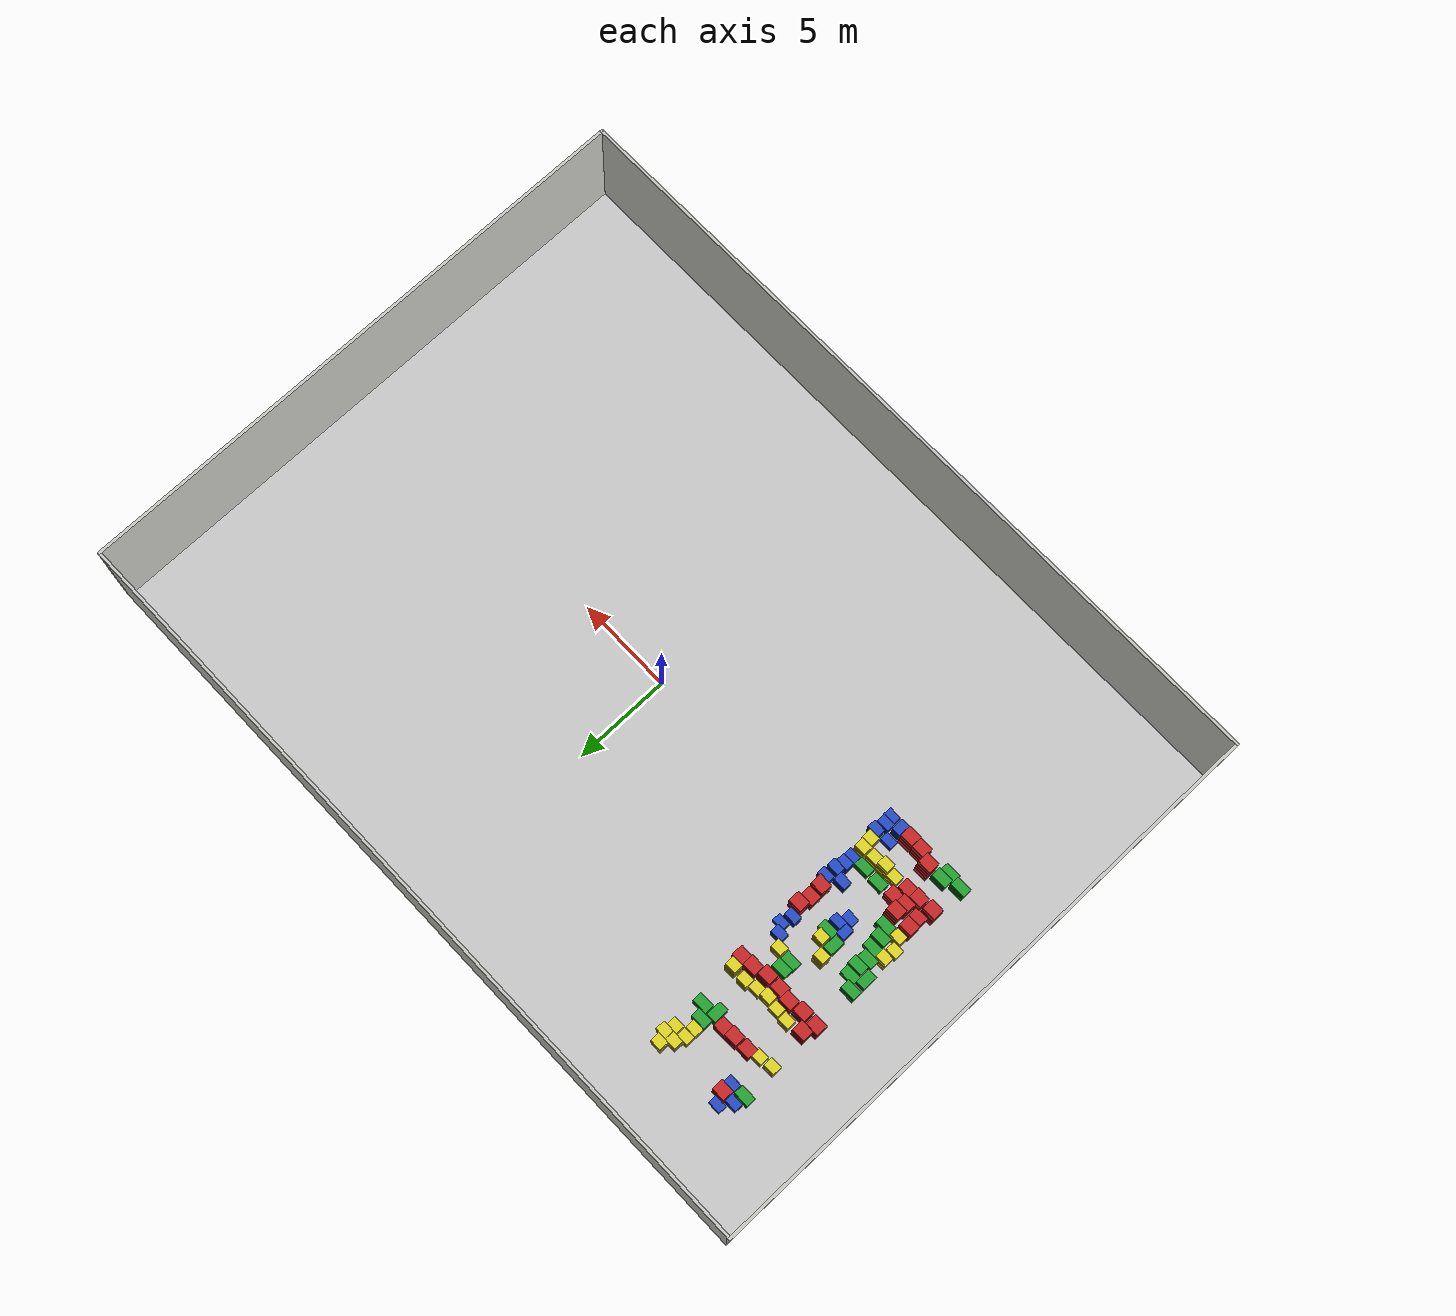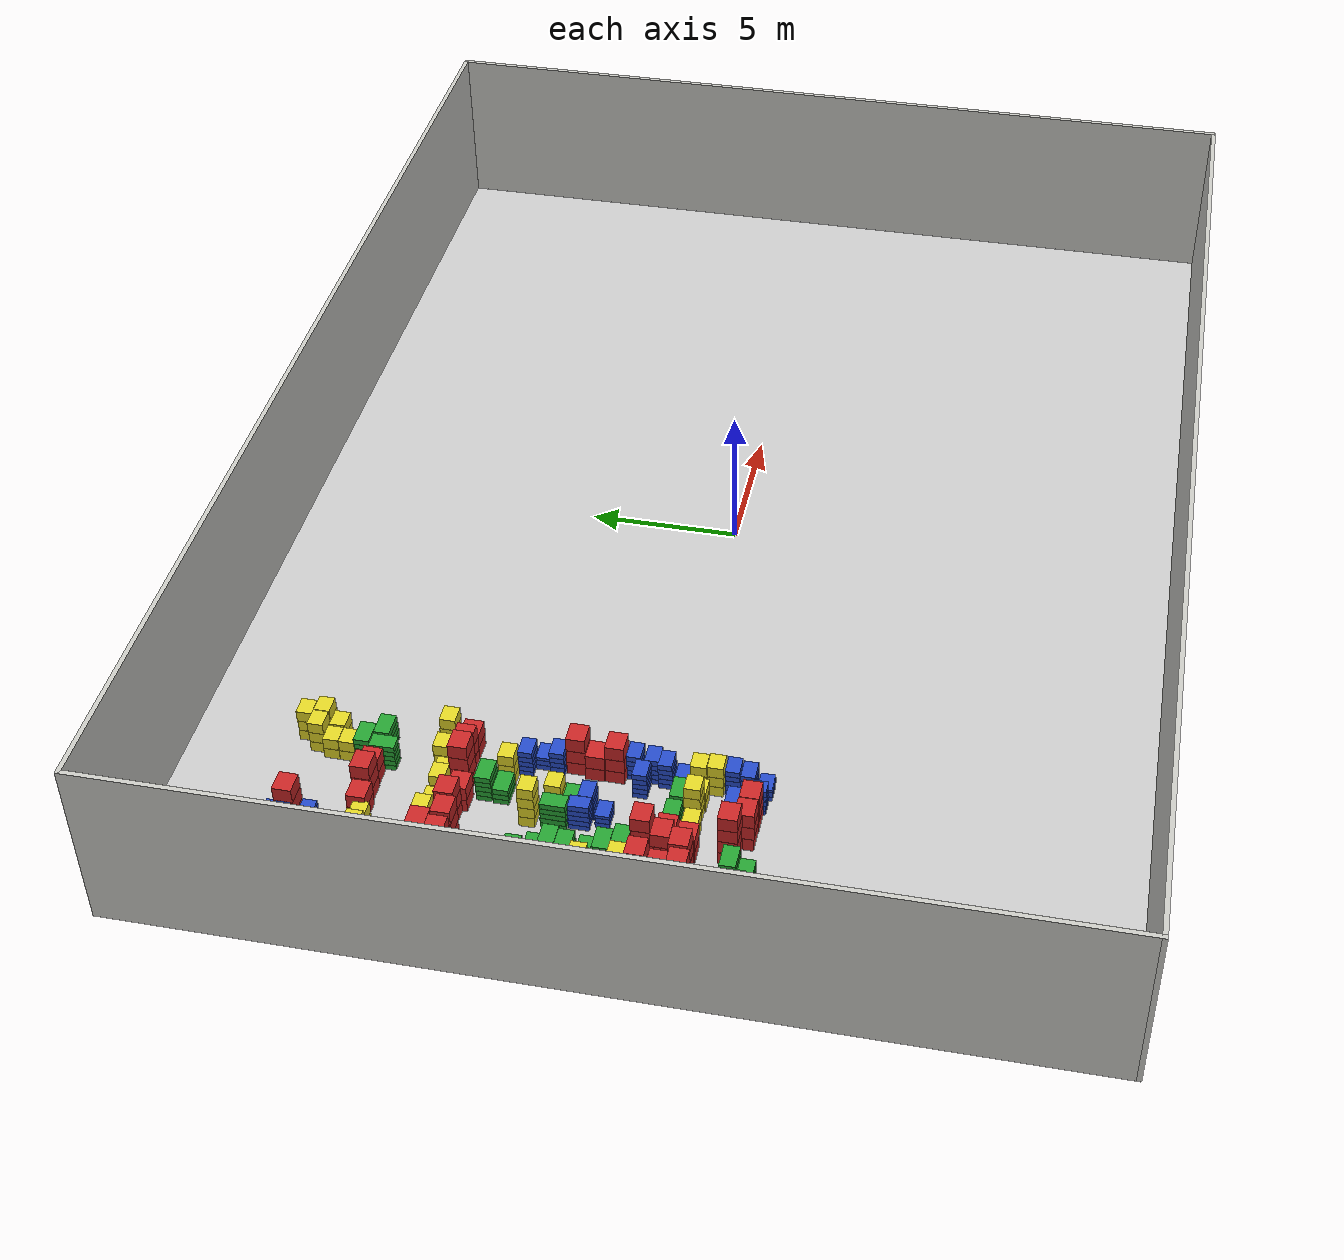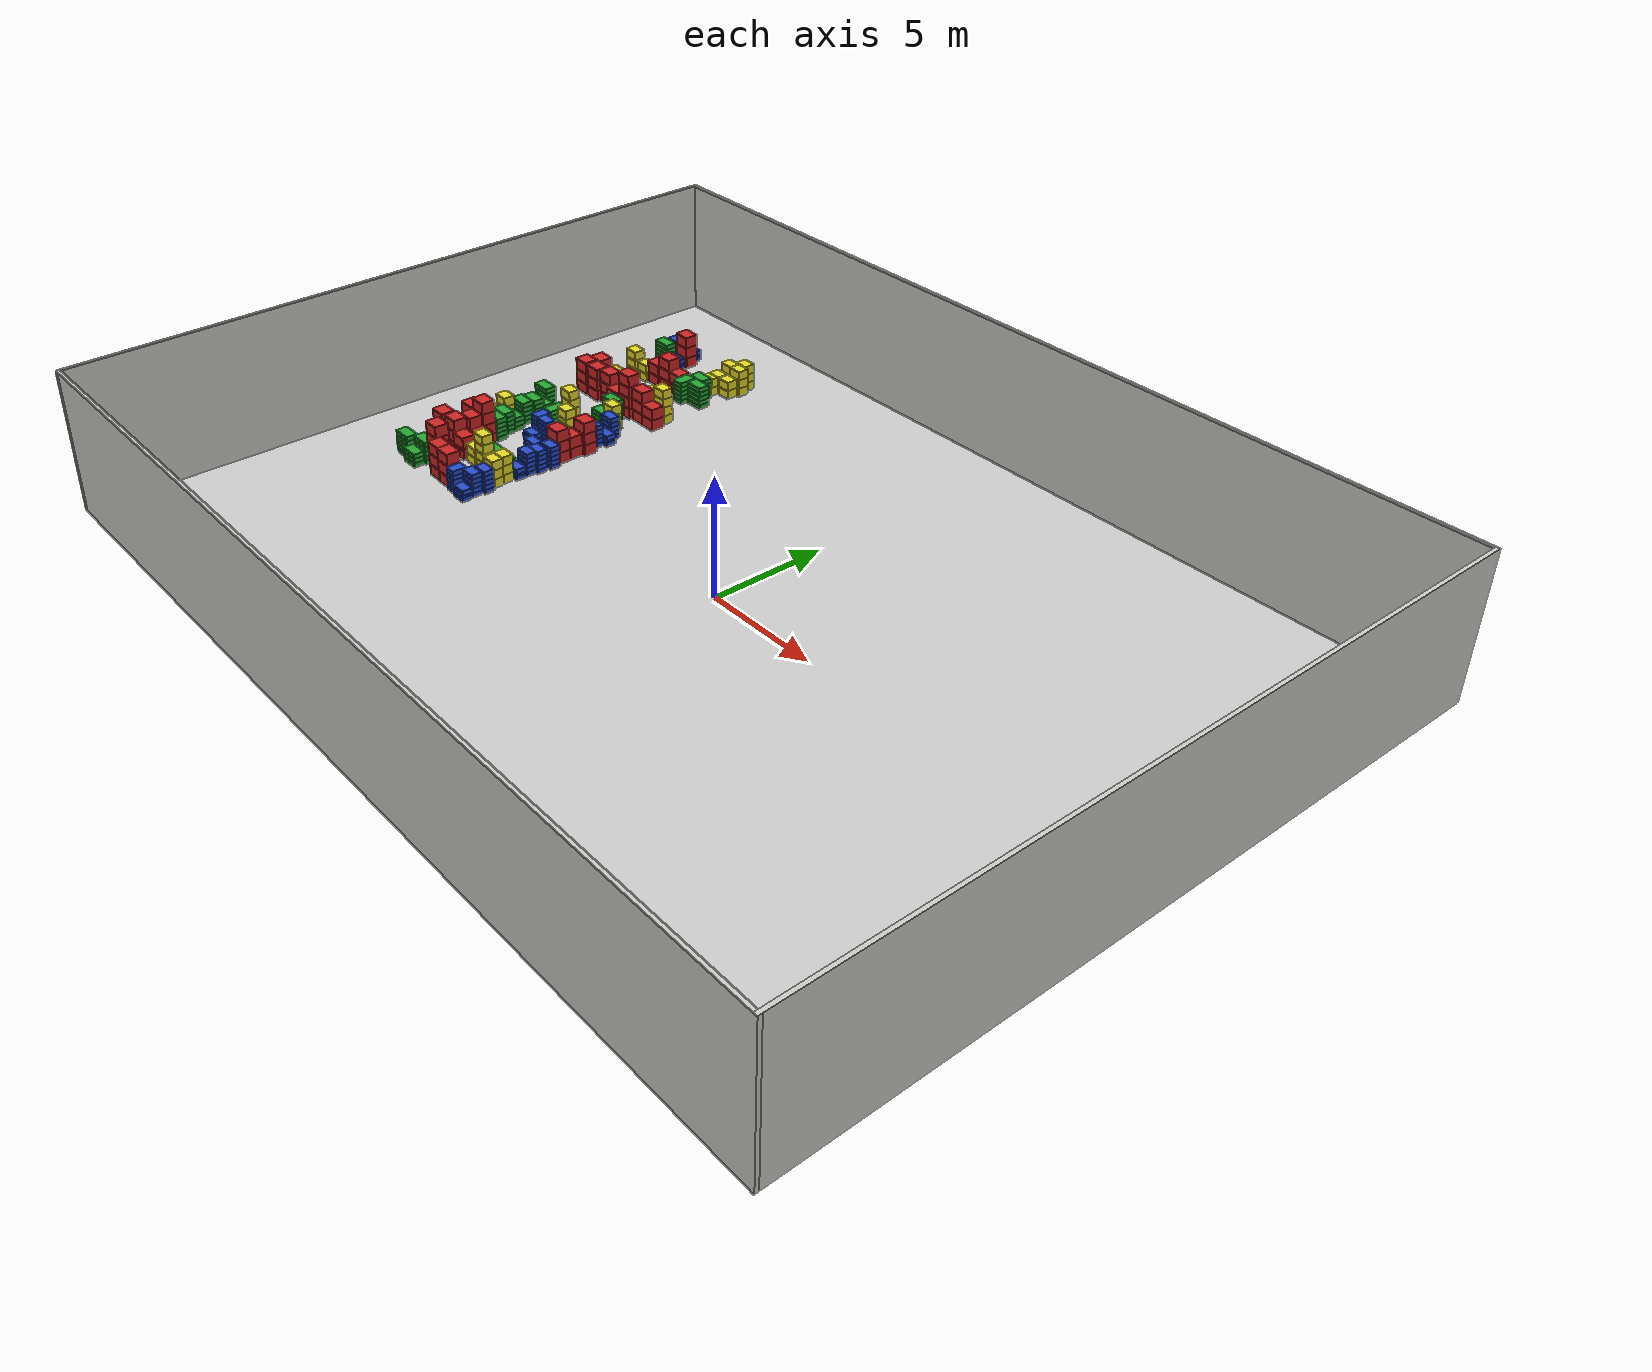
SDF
<sdf version="1.6">
 <world name="default">
  <light name="sun" type="directional">
   <pose>0 0 10 0 -0 0</pose>
   <diffuse>0.8 0.8 0.8 1</diffuse>
   <specular>0.1 0.1 0.1 1</specular>
   <attenuation>
    <range>1000</range>
    <constant>0.9</constant>
    <linear>0.01</linear>
    <quadratic>0.001</quadratic>
   </attenuation>
   <direction>-0.5 0.5 -1</direction>
  </light>
  <model name="factory_floor">
   <static>1</static>
   <link name="link">
    <collision name="collision">
     <geometry><plane><normal>0 0 1</normal><size>40 30</size></plane></geometry>
     <surface><friction><ode><mu>100</mu><mu2>50</mu2></ode></friction></surface>
    </collision>
    <visual name="visual">
     <cast_shadows>0</cast_shadows>
     <geometry><plane><normal>0 0 1</normal><size>40 30</size></plane></geometry>
     <material>
      <script>
       <uri>model://factory_floor/materials/scripts/factory_floor.material</uri>
       <name>FactoryFloor/Image</name>
      </script>
     </material>
    </visual>
   </link>
  </model>
  <model name="floor2">
   <link name="Wall_0">
    <collision name="Wall_0_Collision">
     <geometry><box><size>30.15 0.15 6</size></box></geometry>
     <pose>0 0 3 0 -0 0</pose>
    </collision>
    <visual name="Wall_0_Visual">
     <pose>0 0 3 0 -0 0</pose>
     <geometry><box><size>30.15 0.15 6</size></box></geometry>
     <material>
      <script><uri>file://media/materials/scripts/gazebo.material</uri><name>Gazebo/CeilingTiled</name></script>
      <ambient>1 1 1 1</ambient>
     </material>
    </visual>
    <pose>20 0 0 0 0 -1.5708</pose>
   </link>
   <link name="Wall_1">
    <collision name="Wall_1_Collision">
     <geometry><box><size>40.15 0.15 6</size></box></geometry>
     <pose>0 0 3 0 -0 0</pose>
    </collision>
    <visual name="Wall_1_Visual">
     <pose>0 0 3 0 -0 0</pose>
     <geometry><box><size>40.15 0.15 6</size></box></geometry>
     <material>
      <script><uri>file://media/materials/scripts/gazebo.material</uri><name>Gazebo/CeilingTiled</name></script>
      <ambient>1 1 1 1</ambient>
     </material>
    </visual>
    <pose>0 -15 0 0 -0 3.14159</pose>
   </link>
   <link name="Wall_2">
    <collision name="Wall_2_Collision">
     <geometry><box><size>30.15 0.15 6</size></box></geometry>
     <pose>0 0 3 0 -0 0</pose>
    </collision>
    <visual name="Wall_2_Visual">
     <pose>0 0 3 0 -0 0</pose>
     <geometry><box><size>30.15 0.15 6</size></box></geometry>
     <material>
      <script><uri>file://media/materials/scripts/gazebo.material</uri><name>Gazebo/CeilingTiled</name></script>
      <ambient>1 1 1 1</ambient>
     </material>
    </visual>
    <pose>-20 0 0 0 -0 1.5708</pose>
   </link>
   <link name="Wall_3">
    <collision name="Wall_3_Collision">
     <geometry><box><size>40.15 0.15 6</size></box></geometry>
     <pose>0 0 3 0 -0 0</pose>
    </collision>
    <visual name="Wall_3_Visual">
     <pose>0 0 3 0 -0 0</pose>
     <geometry><box><size>40.15 0.15 6</size></box></geometry>
     <material>
      <script><uri>file://media/materials/scripts/gazebo.material</uri><name>Gazebo/CeilingTiled</name></script>
      <ambient>1 1 1 1</ambient>
     </material>
    </visual>
    <pose>0 15 0 0 -0 0</pose>
   </link>
   <static>1</static>
  </model>
  <gravity>0 0 -9.8</gravity>
  <magnetic_field>6e-06 2.3e-05 -4.2e-05</magnetic_field>
  <atmosphere type="adiabatic"/>
  <physics name="default_physics" default="0" type="ode">
   <max_step_size>0.001</max_step_size>
   <real_time_factor>1</real_time_factor>
   <real_time_update_rate>1000</real_time_update_rate>
  </physics>
  <scene><ambient>0.4 0.4 0.4 1</ambient><background>0.7 0.7 0.7 1</background><shadows>1</shadows></scene>
  <spherical_coordinates>
   <surface_model>EARTH_WGS84</surface_model>
   <latitude_deg>0</latitude_deg>
   <longitude_deg>0</longitude_deg>
   <elevation>0</elevation>
   <heading_deg>0</heading_deg>
  </spherical_coordinates>
  <model name="baggage_D_x5">
   <model name="baggage_D_0">
    <static>1</static>
    <link name="link">
     <collision name="collision"><geometry><box><size>0.8 0.5 0.2</size></box></geometry></collision>
     <visual name="visual">
      <geometry><box><size>0.8 0.5 0.2</size></box></geometry>
      <material>
       <script><uri>file://media/materials/scripts/gazebo.material</uri><name>Gazebo/Green</name></script>
      </material>
     </visual>
    </link>
    <pose>0 0 0.1 0 -0 0</pose>
   </model>
   <model name="baggage_D_1">
    <static>1</static>
    <link name="link">
     <collision name="collision"><geometry><box><size>0.8 0.5 0.2</size></box></geometry></collision>
     <visual name="visual">
      <geometry><box><size>0.8 0.5 0.2</size></box></geometry>
      <material>
       <script><uri>file://media/materials/scripts/gazebo.material</uri><name>Gazebo/Green</name></script>
      </material>
     </visual>
    </link>
    <pose>-0.0065 -0.0092 0.3 0 -0 0</pose>
   </model>
   <model name="baggage_D_2">
    <static>1</static>
    <link name="link">
     <collision name="collision"><geometry><box><size>0.8 0.5 0.2</size></box></geometry></collision>
     <visual name="visual">
      <geometry><box><size>0.8 0.5 0.2</size></box></geometry>
      <material>
       <script><uri>file://media/materials/scripts/gazebo.material</uri><name>Gazebo/Green</name></script>
      </material>
     </visual>
    </link>
    <pose>0.005 -0.0052 0.5 0 -0 0</pose>
   </model>
   <model name="baggage_D_3">
    <static>1</static>
    <link name="link">
     <collision name="collision"><geometry><box><size>0.8 0.5 0.2</size></box></geometry></collision>
     <visual name="visual">
      <geometry><box><size>0.8 0.5 0.2</size></box></geometry>
      <material>
       <script><uri>file://media/materials/scripts/gazebo.material</uri><name>Gazebo/Green</name></script>
      </material>
     </visual>
    </link>
    <pose>0.0074 0.0002 0.7 0 -0 0</pose>
   </model>
   <model name="baggage_D_4">
    <static>1</static>
    <link name="link">
     <collision name="collision"><geometry><box><size>0.8 0.5 0.2</size></box></geometry></collision>
     <visual name="visual">
      <geometry><box><size>0.8 0.5 0.2</size></box></geometry>
      <material>
       <script><uri>file://media/materials/scripts/gazebo.material</uri><name>Gazebo/Green</name></script>
      </material>
     </visual>
    </link>
    <pose>-0.006 0.0081 0.9 0 -0 0</pose>
   </model>
   <pose>-16.0603 -3.09138 0 0 -0 0</pose>
  </model>
  <model name="baggage_D_x5_0">
   <model name="baggage_D_0">
    <static>1</static>
    <link name="link">
     <collision name="collision"><geometry><box><size>0.8 0.5 0.2</size></box></geometry></collision>
     <visual name="visual">
      <geometry><box><size>0.8 0.5 0.2</size></box></geometry>
      <material>
       <script><uri>file://media/materials/scripts/gazebo.material</uri><name>Gazebo/Green</name></script>
      </material>
     </visual>
    </link>
    <pose>0 0 0.1 0 -0 0</pose>
   </model>
   <model name="baggage_D_1">
    <static>1</static>
    <link name="link">
     <collision name="collision"><geometry><box><size>0.8 0.5 0.2</size></box></geometry></collision>
     <visual name="visual">
      <geometry><box><size>0.8 0.5 0.2</size></box></geometry>
      <material>
       <script><uri>file://media/materials/scripts/gazebo.material</uri><name>Gazebo/Green</name></script>
      </material>
     </visual>
    </link>
    <pose>-0.0065 -0.0092 0.3 0 -0 0</pose>
   </model>
   <model name="baggage_D_2">
    <static>1</static>
    <link name="link">
     <collision name="collision"><geometry><box><size>0.8 0.5 0.2</size></box></geometry></collision>
     <visual name="visual">
      <geometry><box><size>0.8 0.5 0.2</size></box></geometry>
      <material>
       <script><uri>file://media/materials/scripts/gazebo.material</uri><name>Gazebo/Green</name></script>
      </material>
     </visual>
    </link>
    <pose>0.005 -0.0052 0.5 0 -0 0</pose>
   </model>
   <model name="baggage_D_3">
    <static>1</static>
    <link name="link">
     <collision name="collision"><geometry><box><size>0.8 0.5 0.2</size></box></geometry></collision>
     <visual name="visual">
      <geometry><box><size>0.8 0.5 0.2</size></box></geometry>
      <material>
       <script><uri>file://media/materials/scripts/gazebo.material</uri><name>Gazebo/Green</name></script>
      </material>
     </visual>
    </link>
    <pose>0.0074 0.0002 0.7 0 -0 0</pose>
   </model>
   <model name="baggage_D_4">
    <static>1</static>
    <link name="link">
     <collision name="collision"><geometry><box><size>0.8 0.5 0.2</size></box></geometry></collision>
     <visual name="visual">
      <geometry><box><size>0.8 0.5 0.2</size></box></geometry>
      <material>
       <script><uri>file://media/materials/scripts/gazebo.material</uri><name>Gazebo/Green</name></script>
      </material>
     </visual>
    </link>
    <pose>-0.006 0.0081 0.9 0 -0 0</pose>
   </model>
   <pose>-15.1916 -2.77971 0 0 -0 0</pose>
  </model>
  <model name="baggage_D_x3">
   <model name="baggage_D_0">
    <static>1</static>
    <link name="link">
     <collision name="collision"><geometry><box><size>0.8 0.5 0.2</size></box></geometry></collision>
     <visual name="visual">
      <geometry><box><size>0.8 0.5 0.2</size></box></geometry>
      <material>
       <script><uri>file://media/materials/scripts/gazebo.material</uri><name>Gazebo/Green</name></script>
      </material>
     </visual>
    </link>
    <pose>0 0 0.1 0 -0 0</pose>
   </model>
   <model name="baggage_D_1">
    <static>1</static>
    <link name="link">
     <collision name="collision"><geometry><box><size>0.8 0.5 0.2</size></box></geometry></collision>
     <visual name="visual">
      <geometry><box><size>0.8 0.5 0.2</size></box></geometry>
      <material>
       <script><uri>file://media/materials/scripts/gazebo.material</uri><name>Gazebo/Green</name></script>
      </material>
     </visual>
    </link>
    <pose>-0.0056 0.0083 0.3 0 -0 0</pose>
   </model>
   <model name="baggage_D_2">
    <static>1</static>
    <link name="link">
     <collision name="collision"><geometry><box><size>0.8 0.5 0.2</size></box></geometry></collision>
     <visual name="visual">
      <geometry><box><size>0.8 0.5 0.2</size></box></geometry>
      <material>
       <script><uri>file://media/materials/scripts/gazebo.material</uri><name>Gazebo/Green</name></script>
      </material>
     </visual>
    </link>
    <pose>0.0053 0.0057 0.5 0 -0 0</pose>
   </model>
   <pose>-15.2783 -3.26087 0 0 -0 0</pose>
  </model>
  <model name="baggage_A_x4">
   <model name="baggage_A_0">
    <static>1</static>
    <link name="link">
     <collision name="collision"><geometry><box><size>0.7 0.6 0.5</size></box></geometry></collision>
     <visual name="visual">
      <geometry><box><size>0.7 0.6 0.5</size></box></geometry>
      <material>
       <script><uri>file://media/materials/scripts/gazebo.material</uri><name>Gazebo/Red</name></script>
      </material>
     </visual>
    </link>
    <pose>0 0 0.25 0 -0 0</pose>
   </model>
   <model name="baggage_A_1">
    <static>1</static>
    <link name="link">
     <collision name="collision"><geometry><box><size>0.7 0.6 0.5</size></box></geometry></collision>
     <visual name="visual">
      <geometry><box><size>0.7 0.6 0.5</size></box></geometry>
      <material>
       <script><uri>file://media/materials/scripts/gazebo.material</uri><name>Gazebo/Red</name></script>
      </material>
     </visual>
    </link>
    <pose>0.0053 0.0033 0.75 0 -0 0</pose>
   </model>
   <model name="baggage_A_2">
    <static>1</static>
    <link name="link">
     <collision name="collision"><geometry><box><size>0.7 0.6 0.5</size></box></geometry></collision>
     <visual name="visual">
      <geometry><box><size>0.7 0.6 0.5</size></box></geometry>
      <material>
       <script><uri>file://media/materials/scripts/gazebo.material</uri><name>Gazebo/Red</name></script>
      </material>
     </visual>
    </link>
    <pose>-0.0056 -0.0003 1.25 0 -0 0</pose>
   </model>
   <model name="baggage_A_3">
    <static>1</static>
    <link name="link">
     <collision name="collision"><geometry><box><size>0.7 0.6 0.5</size></box></geometry></collision>
     <visual name="visual">
      <geometry><box><size>0.7 0.6 0.5</size></box></geometry>
      <material>
       <script><uri>file://media/materials/scripts/gazebo.material</uri><name>Gazebo/Red</name></script>
      </material>
     </visual>
    </link>
    <pose>-0.0098 0.0065 1.75 0 -0 0</pose>
   </model>
   <pose>-14.3613 -2.61485 0 0 -0 0</pose>
  </model>
  <model name="baggage_A_x3">
   <model name="baggage_A_0">
    <static>1</static>
    <link name="link">
     <collision name="collision"><geometry><box><size>0.7 0.6 0.5</size></box></geometry></collision>
     <visual name="visual">
      <geometry><box><size>0.7 0.6 0.5</size></box></geometry>
      <material>
       <script><uri>file://media/materials/scripts/gazebo.material</uri><name>Gazebo/Red</name></script>
      </material>
     </visual>
    </link>
    <pose>0 0 0.25 0 -0 0</pose>
   </model>
   <model name="baggage_A_1">
    <static>1</static>
    <link name="link">
     <collision name="collision"><geometry><box><size>0.7 0.6 0.5</size></box></geometry></collision>
     <visual name="visual">
      <geometry><box><size>0.7 0.6 0.5</size></box></geometry>
      <material>
       <script><uri>file://media/materials/scripts/gazebo.material</uri><name>Gazebo/Red</name></script>
      </material>
     </visual>
    </link>
    <pose>-0.006 -0.0077 0.75 0 -0 0</pose>
   </model>
   <model name="baggage_A_2">
    <static>1</static>
    <link name="link">
     <collision name="collision"><geometry><box><size>0.7 0.6 0.5</size></box></geometry></collision>
     <visual name="visual">
      <geometry><box><size>0.7 0.6 0.5</size></box></geometry>
      <material>
       <script><uri>file://media/materials/scripts/gazebo.material</uri><name>Gazebo/Red</name></script>
      </material>
     </visual>
    </link>
    <pose>0.0045 0.0005 1.25 0 -0 0</pose>
   </model>
   <pose>-13.6814 -2.97255 0 0 -0 0</pose>
  </model>
  <model name="baggage_A_x3_0">
   <model name="baggage_A_0">
    <static>1</static>
    <link name="link">
     <collision name="collision"><geometry><box><size>0.7 0.6 0.5</size></box></geometry></collision>
     <visual name="visual">
      <geometry><box><size>0.7 0.6 0.5</size></box></geometry>
      <material>
       <script><uri>file://media/materials/scripts/gazebo.material</uri><name>Gazebo/Red</name></script>
      </material>
     </visual>
    </link>
    <pose>0 0 0.25 0 -0 0</pose>
   </model>
   <model name="baggage_A_1">
    <static>1</static>
    <link name="link">
     <collision name="collision"><geometry><box><size>0.7 0.6 0.5</size></box></geometry></collision>
     <visual name="visual">
      <geometry><box><size>0.7 0.6 0.5</size></box></geometry>
      <material>
       <script><uri>file://media/materials/scripts/gazebo.material</uri><name>Gazebo/Red</name></script>
      </material>
     </visual>
    </link>
    <pose>-0.006 -0.0077 0.75 0 -0 0</pose>
   </model>
   <model name="baggage_A_2">
    <static>1</static>
    <link name="link">
     <collision name="collision"><geometry><box><size>0.7 0.6 0.5</size></box></geometry></collision>
     <visual name="visual">
      <geometry><box><size>0.7 0.6 0.5</size></box></geometry>
      <material>
       <script><uri>file://media/materials/scripts/gazebo.material</uri><name>Gazebo/Red</name></script>
      </material>
     </visual>
    </link>
    <pose>0.0045 0.0005 1.25 0 -0 0</pose>
   </model>
   <pose>-12.9672 -2.99066 0 0 -0 0</pose>
  </model>
  <model name="baggage_B_x3">
   <model name="baggage_B_0">
    <static>1</static>
    <link name="link">
     <collision name="collision"><geometry><box><size>0.65 0.45 0.2</size></box></geometry></collision>
     <visual name="visual">
      <geometry><box><size>0.65 0.45 0.2</size></box></geometry>
      <material>
       <script><uri>file://media/materials/scripts/gazebo.material</uri><name>Gazebo/Blue</name></script>
      </material>
     </visual>
    </link>
    <pose>0 0 0.1 0 -0 0</pose>
   </model>
   <model name="baggage_B_1">
    <static>1</static>
    <link name="link">
     <collision name="collision"><geometry><box><size>0.65 0.45 0.2</size></box></geometry></collision>
     <visual name="visual">
      <geometry><box><size>0.65 0.45 0.2</size></box></geometry>
      <material>
       <script><uri>file://media/materials/scripts/gazebo.material</uri><name>Gazebo/Blue</name></script>
      </material>
     </visual>
    </link>
    <pose>0.0028 -0.0086 0.3 0 -0 0</pose>
   </model>
   <model name="baggage_B_2">
    <static>1</static>
    <link name="link">
     <collision name="collision"><geometry><box><size>0.65 0.45 0.2</size></box></geometry></collision>
     <visual name="visual">
      <geometry><box><size>0.65 0.45 0.2</size></box></geometry>
      <material>
       <script><uri>file://media/materials/scripts/gazebo.material</uri><name>Gazebo/Blue</name></script>
      </material>
     </visual>
    </link>
    <pose>0.0092 0.006 0.4 0 -0 0</pose>
   </model>
   <pose>-11.6581 -3.23288 0 0 -0 0</pose>
  </model>
  <model name="baggage_B_x5">
   <model name="baggage_B_0">
    <static>1</static>
    <link name="link">
     <collision name="collision"><geometry><box><size>0.65 0.45 0.2</size></box></geometry></collision>
     <visual name="visual">
      <geometry><box><size>0.65 0.45 0.2</size></box></geometry>
      <material>
       <script><uri>file://media/materials/scripts/gazebo.material</uri><name>Gazebo/Blue</name></script>
      </material>
     </visual>
    </link>
    <pose>0 0 0.1 0 -0 0</pose>
   </model>
   <model name="baggage_B_1">
    <static>1</static>
    <link name="link">
     <collision name="collision"><geometry><box><size>0.65 0.45 0.2</size></box></geometry></collision>
     <visual name="visual">
      <geometry><box><size>0.65 0.45 0.2</size></box></geometry>
      <material>
       <script><uri>file://media/materials/scripts/gazebo.material</uri><name>Gazebo/Blue</name></script>
      </material>
     </visual>
    </link>
    <pose>-0.0014 -0.0091 0.3 0 -0 0</pose>
   </model>
   <model name="baggage_B_2">
    <static>1</static>
    <link name="link">
     <collision name="collision"><geometry><box><size>0.65 0.45 0.2</size></box></geometry></collision>
     <visual name="visual">
      <geometry><box><size>0.65 0.45 0.2</size></box></geometry>
      <material>
       <script><uri>file://media/materials/scripts/gazebo.material</uri><name>Gazebo/Blue</name></script>
      </material>
     </visual>
    </link>
    <pose>0.0076 -0.0066 0.5 0 -0 0</pose>
   </model>
   <model name="baggage_B_3">
    <static>1</static>
    <link name="link">
     <collision name="collision"><geometry><box><size>0.65 0.45 0.2</size></box></geometry></collision>
     <visual name="visual">
      <geometry><box><size>0.65 0.45 0.2</size></box></geometry>
      <material>
       <script><uri>file://media/materials/scripts/gazebo.material</uri><name>Gazebo/Blue</name></script>
      </material>
     </visual>
    </link>
    <pose>0 -0.0032 0.7 0 -0 0</pose>
   </model>
   <model name="baggage_B_4">
    <static>1</static>
    <link name="link">
     <collision name="collision"><geometry><box><size>0.65 0.45 0.2</size></box></geometry></collision>
     <visual name="visual">
      <geometry><box><size>0.65 0.45 0.2</size></box></geometry>
      <material>
       <script><uri>file://media/materials/scripts/gazebo.material</uri><name>Gazebo/Blue</name></script>
      </material>
     </visual>
    </link>
    <pose>0.0023 0.0073 0.9 0 -0 0</pose>
   </model>
   <pose>-11.7207 -2.7222 0 0 -0 0</pose>
  </model>
  <model name="baggage_B_x5_0">
   <model name="baggage_B_0">
    <static>1</static>
    <link name="link">
     <collision name="collision"><geometry><box><size>0.65 0.45 0.2</size></box></geometry></collision>
     <visual name="visual">
      <geometry><box><size>0.65 0.45 0.2</size></box></geometry>
      <material>
       <script><uri>file://media/materials/scripts/gazebo.material</uri><name>Gazebo/Blue</name></script>
      </material>
     </visual>
    </link>
    <pose>0 0 0.1 0 -0 0</pose>
   </model>
   <model name="baggage_B_1">
    <static>1</static>
    <link name="link">
     <collision name="collision"><geometry><box><size>0.65 0.45 0.2</size></box></geometry></collision>
     <visual name="visual">
      <geometry><box><size>0.65 0.45 0.2</size></box></geometry>
      <material>
       <script><uri>file://media/materials/scripts/gazebo.material</uri><name>Gazebo/Blue</name></script>
      </material>
     </visual>
    </link>
    <pose>-0.0014 -0.0091 0.3 0 -0 0</pose>
   </model>
   <model name="baggage_B_2">
    <static>1</static>
    <link name="link">
     <collision name="collision"><geometry><box><size>0.65 0.45 0.2</size></box></geometry></collision>
     <visual name="visual">
      <geometry><box><size>0.65 0.45 0.2</size></box></geometry>
      <material>
       <script><uri>file://media/materials/scripts/gazebo.material</uri><name>Gazebo/Blue</name></script>
      </material>
     </visual>
    </link>
    <pose>0.0076 -0.0066 0.5 0 -0 0</pose>
   </model>
   <model name="baggage_B_3">
    <static>1</static>
    <link name="link">
     <collision name="collision"><geometry><box><size>0.65 0.45 0.2</size></box></geometry></collision>
     <visual name="visual">
      <geometry><box><size>0.65 0.45 0.2</size></box></geometry>
      <material>
       <script><uri>file://media/materials/scripts/gazebo.material</uri><name>Gazebo/Blue</name></script>
      </material>
     </visual>
    </link>
    <pose>0 -0.0032 0.7 0 -0 0</pose>
   </model>
   <model name="baggage_B_4">
    <static>1</static>
    <link name="link">
     <collision name="collision"><geometry><box><size>0.65 0.45 0.2</size></box></geometry></collision>
     <visual name="visual">
      <geometry><box><size>0.65 0.45 0.2</size></box></geometry>
      <material>
       <script><uri>file://media/materials/scripts/gazebo.material</uri><name>Gazebo/Blue</name></script>
      </material>
     </visual>
    </link>
    <pose>0.0023 0.0073 0.9 0 -0 0</pose>
   </model>
   <pose>-12.34 -3.04334 0 0 0 -1.57187</pose>
  </model>
  <model name="baggage_A_x3_1">
   <model name="baggage_A_0">
    <static>1</static>
    <link name="link">
     <collision name="collision"><geometry><box><size>0.7 0.6 0.5</size></box></geometry></collision>
     <visual name="visual">
      <geometry><box><size>0.7 0.6 0.5</size></box></geometry>
      <material>
       <script><uri>file://media/materials/scripts/gazebo.material</uri><name>Gazebo/Red</name></script>
      </material>
     </visual>
    </link>
    <pose>0 0 0.25 0 -0 0</pose>
   </model>
   <model name="baggage_A_1">
    <static>1</static>
    <link name="link">
     <collision name="collision"><geometry><box><size>0.7 0.6 0.5</size></box></geometry></collision>
     <visual name="visual">
      <geometry><box><size>0.7 0.6 0.5</size></box></geometry>
      <material>
       <script><uri>file://media/materials/scripts/gazebo.material</uri><name>Gazebo/Red</name></script>
      </material>
     </visual>
    </link>
    <pose>-0.006 -0.0077 0.75 0 -0 0</pose>
   </model>
   <model name="baggage_A_2">
    <static>1</static>
    <link name="link">
     <collision name="collision"><geometry><box><size>0.7 0.6 0.5</size></box></geometry></collision>
     <visual name="visual">
      <geometry><box><size>0.7 0.6 0.5</size></box></geometry>
      <material>
       <script><uri>file://media/materials/scripts/gazebo.material</uri><name>Gazebo/Red</name></script>
      </material>
     </visual>
    </link>
    <pose>0.0045 0.0005 1.25 0 -0 0</pose>
   </model>
   <pose>-15.9557 -1.37192 0 0 -0 0</pose>
  </model>
  <model name="baggage_A_x2">
   <model name="baggage_A_0">
    <static>1</static>
    <link name="link">
     <collision name="collision"><geometry><box><size>0.7 0.6 0.5</size></box></geometry></collision>
     <visual name="visual">
      <geometry><box><size>0.7 0.6 0.5</size></box></geometry>
      <material>
       <script><uri>file://media/materials/scripts/gazebo.material</uri><name>Gazebo/Red</name></script>
      </material>
     </visual>
    </link>
    <pose>0 0 0.25 0 -0 0</pose>
   </model>
   <model name="baggage_A_1">
    <static>1</static>
    <link name="link">
     <collision name="collision"><geometry><box><size>0.7 0.6 0.5</size></box></geometry></collision>
     <visual name="visual">
      <geometry><box><size>0.7 0.6 0.5</size></box></geometry>
      <material>
       <script><uri>file://media/materials/scripts/gazebo.material</uri><name>Gazebo/Red</name></script>
      </material>
     </visual>
    </link>
    <pose>0.0063 -0.0062 0.75 0 -0 0</pose>
   </model>
   <pose>-15.7141 -0.71732 0 0 -0 0</pose>
  </model>
  <model name="baggage_A_x3_2">
   <model name="baggage_A_0">
    <static>1</static>
    <link name="link">
     <collision name="collision"><geometry><box><size>0.7 0.6 0.5</size></box></geometry></collision>
     <visual name="visual">
      <geometry><box><size>0.7 0.6 0.5</size></box></geometry>
      <material>
       <script><uri>file://media/materials/scripts/gazebo.material</uri><name>Gazebo/Red</name></script>
      </material>
     </visual>
    </link>
    <pose>0 0 0.25 0 -0 0</pose>
   </model>
   <model name="baggage_A_1">
    <static>1</static>
    <link name="link">
     <collision name="collision"><geometry><box><size>0.7 0.6 0.5</size></box></geometry></collision>
     <visual name="visual">
      <geometry><box><size>0.7 0.6 0.5</size></box></geometry>
      <material>
       <script><uri>file://media/materials/scripts/gazebo.material</uri><name>Gazebo/Red</name></script>
      </material>
     </visual>
    </link>
    <pose>-0.006 -0.0077 0.75 0 -0 0</pose>
   </model>
   <model name="baggage_A_2">
    <static>1</static>
    <link name="link">
     <collision name="collision"><geometry><box><size>0.7 0.6 0.5</size></box></geometry></collision>
     <visual name="visual">
      <geometry><box><size>0.7 0.6 0.5</size></box></geometry>
      <material>
       <script><uri>file://media/materials/scripts/gazebo.material</uri><name>Gazebo/Red</name></script>
      </material>
     </visual>
    </link>
    <pose>0.0045 0.0005 1.25 0 -0 0</pose>
   </model>
   <pose>-15.7621 -0.111141 0 0 -0 0</pose>
  </model>
  <model name="baggage_A_x3_3">
   <model name="baggage_A_0">
    <static>1</static>
    <link name="link">
     <collision name="collision"><geometry><box><size>0.7 0.6 0.5</size></box></geometry></collision>
     <visual name="visual">
      <geometry><box><size>0.7 0.6 0.5</size></box></geometry>
      <material>
       <script><uri>file://media/materials/scripts/gazebo.material</uri><name>Gazebo/Red</name></script>
      </material>
     </visual>
    </link>
    <pose>0 0 0.25 0 -0 0</pose>
   </model>
   <model name="baggage_A_1">
    <static>1</static>
    <link name="link">
     <collision name="collision"><geometry><box><size>0.7 0.6 0.5</size></box></geometry></collision>
     <visual name="visual">
      <geometry><box><size>0.7 0.6 0.5</size></box></geometry>
      <material>
       <script><uri>file://media/materials/scripts/gazebo.material</uri><name>Gazebo/Red</name></script>
      </material>
     </visual>
    </link>
    <pose>-0.006 -0.0077 0.75 0 -0 0</pose>
   </model>
   <model name="baggage_A_2">
    <static>1</static>
    <link name="link">
     <collision name="collision"><geometry><box><size>0.7 0.6 0.5</size></box></geometry></collision>
     <visual name="visual">
      <geometry><box><size>0.7 0.6 0.5</size></box></geometry>
      <material>
       <script><uri>file://media/materials/scripts/gazebo.material</uri><name>Gazebo/Red</name></script>
      </material>
     </visual>
    </link>
    <pose>0.0045 0.0005 1.25 0 -0 0</pose>
   </model>
   <pose>-14.9333 -0.688455 0 0 -0 0</pose>
  </model>
  <model name="baggage_A_x3_4">
   <model name="baggage_A_0">
    <static>1</static>
    <link name="link">
     <collision name="collision"><geometry><box><size>0.7 0.6 0.5</size></box></geometry></collision>
     <visual name="visual">
      <geometry><box><size>0.7 0.6 0.5</size></box></geometry>
      <material>
       <script><uri>file://media/materials/scripts/gazebo.material</uri><name>Gazebo/Red</name></script>
      </material>
     </visual>
    </link>
    <pose>0 0 0.25 0 -0 0</pose>
   </model>
   <model name="baggage_A_1">
    <static>1</static>
    <link name="link">
     <collision name="collision"><geometry><box><size>0.7 0.6 0.5</size></box></geometry></collision>
     <visual name="visual">
      <geometry><box><size>0.7 0.6 0.5</size></box></geometry>
      <material>
       <script><uri>file://media/materials/scripts/gazebo.material</uri><name>Gazebo/Red</name></script>
      </material>
     </visual>
    </link>
    <pose>-0.006 -0.0077 0.75 0 -0 0</pose>
   </model>
   <model name="baggage_A_2">
    <static>1</static>
    <link name="link">
     <collision name="collision"><geometry><box><size>0.7 0.6 0.5</size></box></geometry></collision>
     <visual name="visual">
      <geometry><box><size>0.7 0.6 0.5</size></box></geometry>
      <material>
       <script><uri>file://media/materials/scripts/gazebo.material</uri><name>Gazebo/Red</name></script>
      </material>
     </visual>
    </link>
    <pose>0.0045 0.0005 1.25 0 -0 0</pose>
   </model>
   <pose>-15.1687 -1.29823 0 0 -0 0</pose>
  </model>
  <model name="baggage_A_x2_0">
   <model name="baggage_A_0">
    <static>1</static>
    <link name="link">
     <collision name="collision"><geometry><box><size>0.7 0.6 0.5</size></box></geometry></collision>
     <visual name="visual">
      <geometry><box><size>0.7 0.6 0.5</size></box></geometry>
      <material>
       <script><uri>file://media/materials/scripts/gazebo.material</uri><name>Gazebo/Red</name></script>
      </material>
     </visual>
    </link>
    <pose>0 0 0.25 0 -0 0</pose>
   </model>
   <model name="baggage_A_1">
    <static>1</static>
    <link name="link">
     <collision name="collision"><geometry><box><size>0.7 0.6 0.5</size></box></geometry></collision>
     <visual name="visual">
      <geometry><box><size>0.7 0.6 0.5</size></box></geometry>
      <material>
       <script><uri>file://media/materials/scripts/gazebo.material</uri><name>Gazebo/Red</name></script>
      </material>
     </visual>
    </link>
    <pose>0.0063 -0.0062 0.75 0 -0 0</pose>
   </model>
   <pose>-14.4926 -1.34813 0 0 -0 0</pose>
  </model>
  <model name="baggage_A_x4_0">
   <model name="baggage_A_0">
    <static>1</static>
    <link name="link">
     <collision name="collision"><geometry><box><size>0.7 0.6 0.5</size></box></geometry></collision>
     <visual name="visual">
      <geometry><box><size>0.7 0.6 0.5</size></box></geometry>
      <material>
       <script><uri>file://media/materials/scripts/gazebo.material</uri><name>Gazebo/Red</name></script>
      </material>
     </visual>
    </link>
    <pose>0 0 0.25 0 -0 0</pose>
   </model>
   <model name="baggage_A_1">
    <static>1</static>
    <link name="link">
     <collision name="collision"><geometry><box><size>0.7 0.6 0.5</size></box></geometry></collision>
     <visual name="visual">
      <geometry><box><size>0.7 0.6 0.5</size></box></geometry>
      <material>
       <script><uri>file://media/materials/scripts/gazebo.material</uri><name>Gazebo/Red</name></script>
      </material>
     </visual>
    </link>
    <pose>0.0053 0.0033 0.75 0 -0 0</pose>
   </model>
   <model name="baggage_A_2">
    <static>1</static>
    <link name="link">
     <collision name="collision"><geometry><box><size>0.7 0.6 0.5</size></box></geometry></collision>
     <visual name="visual">
      <geometry><box><size>0.7 0.6 0.5</size></box></geometry>
      <material>
       <script><uri>file://media/materials/scripts/gazebo.material</uri><name>Gazebo/Red</name></script>
      </material>
     </visual>
    </link>
    <pose>-0.0056 -0.0003 1.25 0 -0 0</pose>
   </model>
   <model name="baggage_A_3">
    <static>1</static>
    <link name="link">
     <collision name="collision"><geometry><box><size>0.7 0.6 0.5</size></box></geometry></collision>
     <visual name="visual">
      <geometry><box><size>0.7 0.6 0.5</size></box></geometry>
      <material>
       <script><uri>file://media/materials/scripts/gazebo.material</uri><name>Gazebo/Red</name></script>
      </material>
     </visual>
    </link>
    <pose>-0.0098 0.0065 1.75 0 -0 0</pose>
   </model>
   <pose>-14.8718 -0.108549 0 0 -0 0</pose>
  </model>
  <model name="baggage_A_x2_1">
   <model name="baggage_A_0">
    <static>1</static>
    <link name="link">
     <collision name="collision"><geometry><box><size>0.7 0.6 0.5</size></box></geometry></collision>
     <visual name="visual">
      <geometry><box><size>0.7 0.6 0.5</size></box></geometry>
      <material>
       <script><uri>file://media/materials/scripts/gazebo.material</uri><name>Gazebo/Red</name></script>
      </material>
     </visual>
    </link>
    <pose>0 0 0.25 0 -0 0</pose>
   </model>
   <model name="baggage_A_1">
    <static>1</static>
    <link name="link">
     <collision name="collision"><geometry><box><size>0.7 0.6 0.5</size></box></geometry></collision>
     <visual name="visual">
      <geometry><box><size>0.7 0.6 0.5</size></box></geometry>
      <material>
       <script><uri>file://media/materials/scripts/gazebo.material</uri><name>Gazebo/Red</name></script>
      </material>
     </visual>
    </link>
    <pose>0.0063 -0.0062 0.75 0 -0 0</pose>
   </model>
   <pose>-14.2882 -0.683416 0 0 -0 0</pose>
  </model>
  <model name="baggage_B_x3_0">
   <model name="baggage_B_0">
    <static>1</static>
    <link name="link">
     <collision name="collision"><geometry><box><size>0.65 0.45 0.2</size></box></geometry></collision>
     <visual name="visual">
      <geometry><box><size>0.65 0.45 0.2</size></box></geometry>
      <material>
       <script><uri>file://media/materials/scripts/gazebo.material</uri><name>Gazebo/Blue</name></script>
      </material>
     </visual>
    </link>
    <pose>0 0 0.1 0 -0 0</pose>
   </model>
   <model name="baggage_B_1">
    <static>1</static>
    <link name="link">
     <collision name="collision"><geometry><box><size>0.65 0.45 0.2</size></box></geometry></collision>
     <visual name="visual">
      <geometry><box><size>0.65 0.45 0.2</size></box></geometry>
      <material>
       <script><uri>file://media/materials/scripts/gazebo.material</uri><name>Gazebo/Blue</name></script>
      </material>
     </visual>
    </link>
    <pose>0.0028 -0.0086 0.3 0 -0 0</pose>
   </model>
   <model name="baggage_B_2">
    <static>1</static>
    <link name="link">
     <collision name="collision"><geometry><box><size>0.65 0.45 0.2</size></box></geometry></collision>
     <visual name="visual">
      <geometry><box><size>0.65 0.45 0.2</size></box></geometry>
      <material>
       <script><uri>file://media/materials/scripts/gazebo.material</uri><name>Gazebo/Blue</name></script>
      </material>
     </visual>
    </link>
    <pose>0.0092 0.006 0.4 0 -0 0</pose>
   </model>
   <pose>-12.3653 -2.347 0 0 -0 0</pose>
  </model>
  <model name="baggage_B_x5_1">
   <model name="baggage_B_0">
    <static>1</static>
    <link name="link">
     <collision name="collision"><geometry><box><size>0.65 0.45 0.2</size></box></geometry></collision>
     <visual name="visual">
      <geometry><box><size>0.65 0.45 0.2</size></box></geometry>
      <material>
       <script><uri>file://media/materials/scripts/gazebo.material</uri><name>Gazebo/Blue</name></script>
      </material>
     </visual>
    </link>
    <pose>0 0 0.1 0 -0 0</pose>
   </model>
   <model name="baggage_B_1">
    <static>1</static>
    <link name="link">
     <collision name="collision"><geometry><box><size>0.65 0.45 0.2</size></box></geometry></collision>
     <visual name="visual">
      <geometry><box><size>0.65 0.45 0.2</size></box></geometry>
      <material>
       <script><uri>file://media/materials/scripts/gazebo.material</uri><name>Gazebo/Blue</name></script>
      </material>
     </visual>
    </link>
    <pose>-0.0014 -0.0091 0.3 0 -0 0</pose>
   </model>
   <model name="baggage_B_2">
    <static>1</static>
    <link name="link">
     <collision name="collision"><geometry><box><size>0.65 0.45 0.2</size></box></geometry></collision>
     <visual name="visual">
      <geometry><box><size>0.65 0.45 0.2</size></box></geometry>
      <material>
       <script><uri>file://media/materials/scripts/gazebo.material</uri><name>Gazebo/Blue</name></script>
      </material>
     </visual>
    </link>
    <pose>0.0076 -0.0066 0.5 0 -0 0</pose>
   </model>
   <model name="baggage_B_3">
    <static>1</static>
    <link name="link">
     <collision name="collision"><geometry><box><size>0.65 0.45 0.2</size></box></geometry></collision>
     <visual name="visual">
      <geometry><box><size>0.65 0.45 0.2</size></box></geometry>
      <material>
       <script><uri>file://media/materials/scripts/gazebo.material</uri><name>Gazebo/Blue</name></script>
      </material>
     </visual>
    </link>
    <pose>0 -0.0032 0.7 0 -0 0</pose>
   </model>
   <model name="baggage_B_4">
    <static>1</static>
    <link name="link">
     <collision name="collision"><geometry><box><size>0.65 0.45 0.2</size></box></geometry></collision>
     <visual name="visual">
      <geometry><box><size>0.65 0.45 0.2</size></box></geometry>
      <material>
       <script><uri>file://media/materials/scripts/gazebo.material</uri><name>Gazebo/Blue</name></script>
      </material>
     </visual>
    </link>
    <pose>0.0023 0.0073 0.9 0 -0 0</pose>
   </model>
   <pose>-11.6217 -2.22105 0 0 -0 0</pose>
  </model>
  <model name="baggage_C_x3">
   <model name="baggage_C_0">
    <static>1</static>
    <link name="link">
     <collision name="collision"><geometry><box><size>0.6 0.5 0.4</size></box></geometry></collision>
     <visual name="visual">
      <geometry><box><size>0.6 0.5 0.4</size></box></geometry>
      <material>
       <script><uri>file://media/materials/scripts/gazebo.material</uri><name>Gazebo/Yellow</name></script>
      </material>
     </visual>
    </link>
    <pose>0 0 0.2 0 -0 0</pose>
   </model>
   <model name="baggage_C_1">
    <static>1</static>
    <link name="link">
     <collision name="collision"><geometry><box><size>0.6 0.5 0.4</size></box></geometry></collision>
     <visual name="visual">
      <geometry><box><size>0.6 0.5 0.4</size></box></geometry>
      <material>
       <script><uri>file://media/materials/scripts/gazebo.material</uri><name>Gazebo/Yellow</name></script>
      </material>
     </visual>
    </link>
    <pose>0.0062 -0.0069 0.6 0 -0 0</pose>
   </model>
   <model name="baggage_C_2">
    <static>1</static>
    <link name="link">
     <collision name="collision"><geometry><box><size>0.6 0.5 0.4</size></box></geometry></collision>
     <visual name="visual">
      <geometry><box><size>0.6 0.5 0.4</size></box></geometry>
      <material>
       <script><uri>file://media/materials/scripts/gazebo.material</uri><name>Gazebo/Yellow</name></script>
      </material>
     </visual>
    </link>
    <pose>0.0089 0.0083 1 0 -0 0</pose>
   </model>
   <pose>-11.7735 -1.71632 0 0 -0 0</pose>
  </model>
  <model name="baggage_C_x3_0">
   <model name="baggage_C_0">
    <static>1</static>
    <link name="link">
     <collision name="collision"><geometry><box><size>0.6 0.5 0.4</size></box></geometry></collision>
     <visual name="visual">
      <geometry><box><size>0.6 0.5 0.4</size></box></geometry>
      <material>
       <script><uri>file://media/materials/scripts/gazebo.material</uri><name>Gazebo/Yellow</name></script>
      </material>
     </visual>
    </link>
    <pose>0 0 0.2 0 -0 0</pose>
   </model>
   <model name="baggage_C_1">
    <static>1</static>
    <link name="link">
     <collision name="collision"><geometry><box><size>0.6 0.5 0.4</size></box></geometry></collision>
     <visual name="visual">
      <geometry><box><size>0.6 0.5 0.4</size></box></geometry>
      <material>
       <script><uri>file://media/materials/scripts/gazebo.material</uri><name>Gazebo/Yellow</name></script>
      </material>
     </visual>
    </link>
    <pose>0.0062 -0.0069 0.6 0 -0 0</pose>
   </model>
   <model name="baggage_C_2">
    <static>1</static>
    <link name="link">
     <collision name="collision"><geometry><box><size>0.6 0.5 0.4</size></box></geometry></collision>
     <visual name="visual">
      <geometry><box><size>0.6 0.5 0.4</size></box></geometry>
      <material>
       <script><uri>file://media/materials/scripts/gazebo.material</uri><name>Gazebo/Yellow</name></script>
      </material>
     </visual>
    </link>
    <pose>0.0089 0.0083 1 0 -0 0</pose>
   </model>
   <pose>-11.8281 -1.20127 0 0 -0 0</pose>
  </model>
  <model name="baggage_C_x2">
   <model name="baggage_C_0">
    <static>1</static>
    <link name="link">
     <collision name="collision"><geometry><box><size>0.6 0.5 0.4</size></box></geometry></collision>
     <visual name="visual">
      <geometry><box><size>0.6 0.5 0.4</size></box></geometry>
      <material>
       <script><uri>file://media/materials/scripts/gazebo.material</uri><name>Gazebo/Yellow</name></script>
      </material>
     </visual>
    </link>
    <pose>0 0 0.2 0 -0 0</pose>
   </model>
   <model name="baggage_C_1">
    <static>1</static>
    <link name="link">
     <collision name="collision"><geometry><box><size>0.6 0.5 0.4</size></box></geometry></collision>
     <visual name="visual">
      <geometry><box><size>0.6 0.5 0.4</size></box></geometry>
      <material>
       <script><uri>file://media/materials/scripts/gazebo.material</uri><name>Gazebo/Yellow</name></script>
      </material>
     </visual>
    </link>
    <pose>0.0093 -0.002 0.6 0 -0 0</pose>
   </model>
   <pose>-12.4698 -1.30971 0 0 -0 0</pose>
  </model>
  <model name="baggage_C_x4">
   <model name="baggage_C_0">
    <static>1</static>
    <link name="link">
     <collision name="collision"><geometry><box><size>0.6 0.5 0.4</size></box></geometry></collision>
     <visual name="visual">
      <geometry><box><size>0.6 0.5 0.4</size></box></geometry>
      <material>
       <script><uri>file://media/materials/scripts/gazebo.material</uri><name>Gazebo/Yellow</name></script>
      </material>
     </visual>
    </link>
    <pose>0 0 0.2 0 -0 0</pose>
   </model>
   <model name="baggage_C_1">
    <static>1</static>
    <link name="link">
     <collision name="collision"><geometry><box><size>0.6 0.5 0.4</size></box></geometry></collision>
     <visual name="visual">
      <geometry><box><size>0.6 0.5 0.4</size></box></geometry>
      <material>
       <script><uri>file://media/materials/scripts/gazebo.material</uri><name>Gazebo/Yellow</name></script>
      </material>
     </visual>
    </link>
    <pose>0.0008 -0.0083 0.6 0 -0 0</pose>
   </model>
   <model name="baggage_C_2">
    <static>1</static>
    <link name="link">
     <collision name="collision"><geometry><box><size>0.6 0.5 0.4</size></box></geometry></collision>
     <visual name="visual">
      <geometry><box><size>0.6 0.5 0.4</size></box></geometry>
      <material>
       <script><uri>file://media/materials/scripts/gazebo.material</uri><name>Gazebo/Yellow</name></script>
      </material>
     </visual>
    </link>
    <pose>0.0001 0.0014 1 0 -0 0</pose>
   </model>
   <model name="baggage_C_3">
    <static>1</static>
    <link name="link">
     <collision name="collision"><geometry><box><size>0.6 0.5 0.4</size></box></geometry></collision>
     <visual name="visual">
      <geometry><box><size>0.6 0.5 0.4</size></box></geometry>
      <material>
       <script><uri>file://media/materials/scripts/gazebo.material</uri><name>Gazebo/Yellow</name></script>
      </material>
     </visual>
    </link>
    <pose>0.007 -0.0089 1.4 0 -0 0</pose>
   </model>
   <pose>-13.1083 -1.26847 0 0 -0 0</pose>
  </model>
  <model name="baggage_C_x2_0">
   <model name="baggage_C_0">
    <static>1</static>
    <link name="link">
     <collision name="collision"><geometry><box><size>0.6 0.5 0.4</size></box></geometry></collision>
     <visual name="visual">
      <geometry><box><size>0.6 0.5 0.4</size></box></geometry>
      <material>
       <script><uri>file://media/materials/scripts/gazebo.material</uri><name>Gazebo/Yellow</name></script>
      </material>
     </visual>
    </link>
    <pose>0 0 0.2 0 -0 0</pose>
   </model>
   <model name="baggage_C_1">
    <static>1</static>
    <link name="link">
     <collision name="collision"><geometry><box><size>0.6 0.5 0.4</size></box></geometry></collision>
     <visual name="visual">
      <geometry><box><size>0.6 0.5 0.4</size></box></geometry>
      <material>
       <script><uri>file://media/materials/scripts/gazebo.material</uri><name>Gazebo/Yellow</name></script>
      </material>
     </visual>
    </link>
    <pose>0.0093 -0.002 0.6 0 -0 0</pose>
   </model>
   <pose>-13.721 -1.31855 0 0 -0 0</pose>
  </model>
  <model name="baggage_C_x3_1">
   <model name="baggage_C_0">
    <static>1</static>
    <link name="link">
     <collision name="collision"><geometry><box><size>0.6 0.5 0.4</size></box></geometry></collision>
     <visual name="visual">
      <geometry><box><size>0.6 0.5 0.4</size></box></geometry>
      <material>
       <script><uri>file://media/materials/scripts/gazebo.material</uri><name>Gazebo/Yellow</name></script>
      </material>
     </visual>
    </link>
    <pose>0 0 0.2 0 -0 0</pose>
   </model>
   <model name="baggage_C_1">
    <static>1</static>
    <link name="link">
     <collision name="collision"><geometry><box><size>0.6 0.5 0.4</size></box></geometry></collision>
     <visual name="visual">
      <geometry><box><size>0.6 0.5 0.4</size></box></geometry>
      <material>
       <script><uri>file://media/materials/scripts/gazebo.material</uri><name>Gazebo/Yellow</name></script>
      </material>
     </visual>
    </link>
    <pose>0.0062 -0.0069 0.6 0 -0 0</pose>
   </model>
   <model name="baggage_C_2">
    <static>1</static>
    <link name="link">
     <collision name="collision"><geometry><box><size>0.6 0.5 0.4</size></box></geometry></collision>
     <visual name="visual">
      <geometry><box><size>0.6 0.5 0.4</size></box></geometry>
      <material>
       <script><uri>file://media/materials/scripts/gazebo.material</uri><name>Gazebo/Yellow</name></script>
      </material>
     </visual>
    </link>
    <pose>0.0089 0.0083 1 0 -0 0</pose>
   </model>
   <pose>-15.7532 0.485614 0 0 -0 0</pose>
  </model>
  <model name="baggage_D_x5_1">
   <model name="baggage_D_0">
    <static>1</static>
    <link name="link">
     <collision name="collision"><geometry><box><size>0.8 0.5 0.2</size></box></geometry></collision>
     <visual name="visual">
      <geometry><box><size>0.8 0.5 0.2</size></box></geometry>
      <material>
       <script><uri>file://media/materials/scripts/gazebo.material</uri><name>Gazebo/Green</name></script>
      </material>
     </visual>
    </link>
    <pose>0 0 0.1 0 -0 0</pose>
   </model>
   <model name="baggage_D_1">
    <static>1</static>
    <link name="link">
     <collision name="collision"><geometry><box><size>0.8 0.5 0.2</size></box></geometry></collision>
     <visual name="visual">
      <geometry><box><size>0.8 0.5 0.2</size></box></geometry>
      <material>
       <script><uri>file://media/materials/scripts/gazebo.material</uri><name>Gazebo/Green</name></script>
      </material>
     </visual>
    </link>
    <pose>-0.0065 -0.0092 0.3 0 -0 0</pose>
   </model>
   <model name="baggage_D_2">
    <static>1</static>
    <link name="link">
     <collision name="collision"><geometry><box><size>0.8 0.5 0.2</size></box></geometry></collision>
     <visual name="visual">
      <geometry><box><size>0.8 0.5 0.2</size></box></geometry>
      <material>
       <script><uri>file://media/materials/scripts/gazebo.material</uri><name>Gazebo/Green</name></script>
      </material>
     </visual>
    </link>
    <pose>0.005 -0.0052 0.5 0 -0 0</pose>
   </model>
   <model name="baggage_D_3">
    <static>1</static>
    <link name="link">
     <collision name="collision"><geometry><box><size>0.8 0.5 0.2</size></box></geometry></collision>
     <visual name="visual">
      <geometry><box><size>0.8 0.5 0.2</size></box></geometry>
      <material>
       <script><uri>file://media/materials/scripts/gazebo.material</uri><name>Gazebo/Green</name></script>
      </material>
     </visual>
    </link>
    <pose>0.0074 0.0002 0.7 0 -0 0</pose>
   </model>
   <model name="baggage_D_4">
    <static>1</static>
    <link name="link">
     <collision name="collision"><geometry><box><size>0.8 0.5 0.2</size></box></geometry></collision>
     <visual name="visual">
      <geometry><box><size>0.8 0.5 0.2</size></box></geometry>
      <material>
       <script><uri>file://media/materials/scripts/gazebo.material</uri><name>Gazebo/Green</name></script>
      </material>
     </visual>
    </link>
    <pose>-0.006 0.0081 0.9 0 -0 0</pose>
   </model>
   <pose>-14.9923 0.523276 0 0 -0 0</pose>
  </model>
  <model name="baggage_B_x3_1">
   <model name="baggage_B_0">
    <static>1</static>
    <link name="link">
     <collision name="collision"><geometry><box><size>0.65 0.45 0.2</size></box></geometry></collision>
     <visual name="visual">
      <geometry><box><size>0.65 0.45 0.2</size></box></geometry>
      <material>
       <script><uri>file://media/materials/scripts/gazebo.material</uri><name>Gazebo/Blue</name></script>
      </material>
     </visual>
    </link>
    <pose>0 0 0.1 0 -0 0</pose>
   </model>
   <model name="baggage_B_1">
    <static>1</static>
    <link name="link">
     <collision name="collision"><geometry><box><size>0.65 0.45 0.2</size></box></geometry></collision>
     <visual name="visual">
      <geometry><box><size>0.65 0.45 0.2</size></box></geometry>
      <material>
       <script><uri>file://media/materials/scripts/gazebo.material</uri><name>Gazebo/Blue</name></script>
      </material>
     </visual>
    </link>
    <pose>0.0028 -0.0086 0.3 0 -0 0</pose>
   </model>
   <model name="baggage_B_2">
    <static>1</static>
    <link name="link">
     <collision name="collision"><geometry><box><size>0.65 0.45 0.2</size></box></geometry></collision>
     <visual name="visual">
      <geometry><box><size>0.65 0.45 0.2</size></box></geometry>
      <material>
       <script><uri>file://media/materials/scripts/gazebo.material</uri><name>Gazebo/Blue</name></script>
      </material>
     </visual>
    </link>
    <pose>0.0092 0.006 0.4 0 -0 0</pose>
   </model>
   <pose>-11.732 -0.670798 0 0 -0 0</pose>
  </model>
  <model name="baggage_B_x5_2">
   <model name="baggage_B_0">
    <static>1</static>
    <link name="link">
     <collision name="collision"><geometry><box><size>0.65 0.45 0.2</size></box></geometry></collision>
     <visual name="visual">
      <geometry><box><size>0.65 0.45 0.2</size></box></geometry>
      <material>
       <script><uri>file://media/materials/scripts/gazebo.material</uri><name>Gazebo/Blue</name></script>
      </material>
     </visual>
    </link>
    <pose>0 0 0.1 0 -0 0</pose>
   </model>
   <model name="baggage_B_1">
    <static>1</static>
    <link name="link">
     <collision name="collision"><geometry><box><size>0.65 0.45 0.2</size></box></geometry></collision>
     <visual name="visual">
      <geometry><box><size>0.65 0.45 0.2</size></box></geometry>
      <material>
       <script><uri>file://media/materials/scripts/gazebo.material</uri><name>Gazebo/Blue</name></script>
      </material>
     </visual>
    </link>
    <pose>-0.0014 -0.0091 0.3 0 -0 0</pose>
   </model>
   <model name="baggage_B_2">
    <static>1</static>
    <link name="link">
     <collision name="collision"><geometry><box><size>0.65 0.45 0.2</size></box></geometry></collision>
     <visual name="visual">
      <geometry><box><size>0.65 0.45 0.2</size></box></geometry>
      <material>
       <script><uri>file://media/materials/scripts/gazebo.material</uri><name>Gazebo/Blue</name></script>
      </material>
     </visual>
    </link>
    <pose>0.0076 -0.0066 0.5 0 -0 0</pose>
   </model>
   <model name="baggage_B_3">
    <static>1</static>
    <link name="link">
     <collision name="collision"><geometry><box><size>0.65 0.45 0.2</size></box></geometry></collision>
     <visual name="visual">
      <geometry><box><size>0.65 0.45 0.2</size></box></geometry>
      <material>
       <script><uri>file://media/materials/scripts/gazebo.material</uri><name>Gazebo/Blue</name></script>
      </material>
     </visual>
    </link>
    <pose>0 -0.0032 0.7 0 -0 0</pose>
   </model>
   <model name="baggage_B_4">
    <static>1</static>
    <link name="link">
     <collision name="collision"><geometry><box><size>0.65 0.45 0.2</size></box></geometry></collision>
     <visual name="visual">
      <geometry><box><size>0.65 0.45 0.2</size></box></geometry>
      <material>
       <script><uri>file://media/materials/scripts/gazebo.material</uri><name>Gazebo/Blue</name></script>
      </material>
     </visual>
    </link>
    <pose>0.0023 0.0073 0.9 0 -0 0</pose>
   </model>
   <pose>-11.7456 -0.151198 0 0 -0 0</pose>
  </model>
  <model name="baggage_B_x5_3">
   <model name="baggage_B_0">
    <static>1</static>
    <link name="link">
     <collision name="collision"><geometry><box><size>0.65 0.45 0.2</size></box></geometry></collision>
     <visual name="visual">
      <geometry><box><size>0.65 0.45 0.2</size></box></geometry>
      <material>
       <script><uri>file://media/materials/scripts/gazebo.material</uri><name>Gazebo/Blue</name></script>
      </material>
     </visual>
    </link>
    <pose>0 0 0.1 0 -0 0</pose>
   </model>
   <model name="baggage_B_1">
    <static>1</static>
    <link name="link">
     <collision name="collision"><geometry><box><size>0.65 0.45 0.2</size></box></geometry></collision>
     <visual name="visual">
      <geometry><box><size>0.65 0.45 0.2</size></box></geometry>
      <material>
       <script><uri>file://media/materials/scripts/gazebo.material</uri><name>Gazebo/Blue</name></script>
      </material>
     </visual>
    </link>
    <pose>-0.0014 -0.0091 0.3 0 -0 0</pose>
   </model>
   <model name="baggage_B_2">
    <static>1</static>
    <link name="link">
     <collision name="collision"><geometry><box><size>0.65 0.45 0.2</size></box></geometry></collision>
     <visual name="visual">
      <geometry><box><size>0.65 0.45 0.2</size></box></geometry>
      <material>
       <script><uri>file://media/materials/scripts/gazebo.material</uri><name>Gazebo/Blue</name></script>
      </material>
     </visual>
    </link>
    <pose>0.0076 -0.0066 0.5 0 -0 0</pose>
   </model>
   <model name="baggage_B_3">
    <static>1</static>
    <link name="link">
     <collision name="collision"><geometry><box><size>0.65 0.45 0.2</size></box></geometry></collision>
     <visual name="visual">
      <geometry><box><size>0.65 0.45 0.2</size></box></geometry>
      <material>
       <script><uri>file://media/materials/scripts/gazebo.material</uri><name>Gazebo/Blue</name></script>
      </material>
     </visual>
    </link>
    <pose>0 -0.0032 0.7 0 -0 0</pose>
   </model>
   <model name="baggage_B_4">
    <static>1</static>
    <link name="link">
     <collision name="collision"><geometry><box><size>0.65 0.45 0.2</size></box></geometry></collision>
     <visual name="visual">
      <geometry><box><size>0.65 0.45 0.2</size></box></geometry>
      <material>
       <script><uri>file://media/materials/scripts/gazebo.material</uri><name>Gazebo/Blue</name></script>
      </material>
     </visual>
    </link>
    <pose>0.0023 0.0073 0.9 0 -0 0</pose>
   </model>
   <pose>-11.6263 0.282143 0 0 -0 0</pose>
  </model>
  <model name="baggage_D_x3_0">
   <model name="baggage_D_0">
    <static>1</static>
    <link name="link">
     <collision name="collision"><geometry><box><size>0.8 0.5 0.2</size></box></geometry></collision>
     <visual name="visual">
      <geometry><box><size>0.8 0.5 0.2</size></box></geometry>
      <material>
       <script><uri>file://media/materials/scripts/gazebo.material</uri><name>Gazebo/Green</name></script>
      </material>
     </visual>
    </link>
    <pose>0 0 0.1 0 -0 0</pose>
   </model>
   <model name="baggage_D_1">
    <static>1</static>
    <link name="link">
     <collision name="collision"><geometry><box><size>0.8 0.5 0.2</size></box></geometry></collision>
     <visual name="visual">
      <geometry><box><size>0.8 0.5 0.2</size></box></geometry>
      <material>
       <script><uri>file://media/materials/scripts/gazebo.material</uri><name>Gazebo/Green</name></script>
      </material>
     </visual>
    </link>
    <pose>-0.0056 0.0083 0.3 0 -0 0</pose>
   </model>
   <model name="baggage_D_2">
    <static>1</static>
    <link name="link">
     <collision name="collision"><geometry><box><size>0.8 0.5 0.2</size></box></geometry></collision>
     <visual name="visual">
      <geometry><box><size>0.8 0.5 0.2</size></box></geometry>
      <material>
       <script><uri>file://media/materials/scripts/gazebo.material</uri><name>Gazebo/Green</name></script>
      </material>
     </visual>
    </link>
    <pose>0.0053 0.0057 0.5 0 -0 0</pose>
   </model>
   <pose>-12.466 -0.703041 0 0 -0 0</pose>
  </model>
  <model name="baggage_D_x3_1">
   <model name="baggage_D_0">
    <static>1</static>
    <link name="link">
     <collision name="collision"><geometry><box><size>0.8 0.5 0.2</size></box></geometry></collision>
     <visual name="visual">
      <geometry><box><size>0.8 0.5 0.2</size></box></geometry>
      <material>
       <script><uri>file://media/materials/scripts/gazebo.material</uri><name>Gazebo/Green</name></script>
      </material>
     </visual>
    </link>
    <pose>0 0 0.1 0 -0 0</pose>
   </model>
   <model name="baggage_D_1">
    <static>1</static>
    <link name="link">
     <collision name="collision"><geometry><box><size>0.8 0.5 0.2</size></box></geometry></collision>
     <visual name="visual">
      <geometry><box><size>0.8 0.5 0.2</size></box></geometry>
      <material>
       <script><uri>file://media/materials/scripts/gazebo.material</uri><name>Gazebo/Green</name></script>
      </material>
     </visual>
    </link>
    <pose>-0.0056 0.0083 0.3 0 -0 0</pose>
   </model>
   <model name="baggage_D_2">
    <static>1</static>
    <link name="link">
     <collision name="collision"><geometry><box><size>0.8 0.5 0.2</size></box></geometry></collision>
     <visual name="visual">
      <geometry><box><size>0.8 0.5 0.2</size></box></geometry>
      <material>
       <script><uri>file://media/materials/scripts/gazebo.material</uri><name>Gazebo/Green</name></script>
      </material>
     </visual>
    </link>
    <pose>0.0053 0.0057 0.5 0 -0 0</pose>
   </model>
   <pose>-13.376 -0.65813 0 0 -0 0</pose>
  </model>
  <model name="baggage_B_x5_4">
   <model name="baggage_B_0">
    <static>1</static>
    <link name="link">
     <collision name="collision"><geometry><box><size>0.65 0.45 0.2</size></box></geometry></collision>
     <visual name="visual">
      <geometry><box><size>0.65 0.45 0.2</size></box></geometry>
      <material>
       <script><uri>file://media/materials/scripts/gazebo.material</uri><name>Gazebo/Blue</name></script>
      </material>
     </visual>
    </link>
    <pose>0 0 0.1 0 -0 0</pose>
   </model>
   <model name="baggage_B_1">
    <static>1</static>
    <link name="link">
     <collision name="collision"><geometry><box><size>0.65 0.45 0.2</size></box></geometry></collision>
     <visual name="visual">
      <geometry><box><size>0.65 0.45 0.2</size></box></geometry>
      <material>
       <script><uri>file://media/materials/scripts/gazebo.material</uri><name>Gazebo/Blue</name></script>
      </material>
     </visual>
    </link>
    <pose>-0.0014 -0.0091 0.3 0 -0 0</pose>
   </model>
   <model name="baggage_B_2">
    <static>1</static>
    <link name="link">
     <collision name="collision"><geometry><box><size>0.65 0.45 0.2</size></box></geometry></collision>
     <visual name="visual">
      <geometry><box><size>0.65 0.45 0.2</size></box></geometry>
      <material>
       <script><uri>file://media/materials/scripts/gazebo.material</uri><name>Gazebo/Blue</name></script>
      </material>
     </visual>
    </link>
    <pose>0.0076 -0.0066 0.5 0 -0 0</pose>
   </model>
   <model name="baggage_B_3">
    <static>1</static>
    <link name="link">
     <collision name="collision"><geometry><box><size>0.65 0.45 0.2</size></box></geometry></collision>
     <visual name="visual">
      <geometry><box><size>0.65 0.45 0.2</size></box></geometry>
      <material>
       <script><uri>file://media/materials/scripts/gazebo.material</uri><name>Gazebo/Blue</name></script>
      </material>
     </visual>
    </link>
    <pose>0 -0.0032 0.7 0 -0 0</pose>
   </model>
   <model name="baggage_B_4">
    <static>1</static>
    <link name="link">
     <collision name="collision"><geometry><box><size>0.65 0.45 0.2</size></box></geometry></collision>
     <visual name="visual">
      <geometry><box><size>0.65 0.45 0.2</size></box></geometry>
      <material>
       <script><uri>file://media/materials/scripts/gazebo.material</uri><name>Gazebo/Blue</name></script>
      </material>
     </visual>
    </link>
    <pose>0.0023 0.0073 0.9 0 -0 0</pose>
   </model>
   <pose>-12.2809 0.527943 0 0 -0 0</pose>
  </model>
  <model name="baggage_B_x5_5">
   <model name="baggage_B_0">
    <static>1</static>
    <link name="link">
     <collision name="collision"><geometry><box><size>0.65 0.45 0.2</size></box></geometry></collision>
     <visual name="visual">
      <geometry><box><size>0.65 0.45 0.2</size></box></geometry>
      <material>
       <script><uri>file://media/materials/scripts/gazebo.material</uri><name>Gazebo/Blue</name></script>
      </material>
     </visual>
    </link>
    <pose>0 0 0.1 0 -0 0</pose>
   </model>
   <model name="baggage_B_1">
    <static>1</static>
    <link name="link">
     <collision name="collision"><geometry><box><size>0.65 0.45 0.2</size></box></geometry></collision>
     <visual name="visual">
      <geometry><box><size>0.65 0.45 0.2</size></box></geometry>
      <material>
       <script><uri>file://media/materials/scripts/gazebo.material</uri><name>Gazebo/Blue</name></script>
      </material>
     </visual>
    </link>
    <pose>-0.0014 -0.0091 0.3 0 -0 0</pose>
   </model>
   <model name="baggage_B_2">
    <static>1</static>
    <link name="link">
     <collision name="collision"><geometry><box><size>0.65 0.45 0.2</size></box></geometry></collision>
     <visual name="visual">
      <geometry><box><size>0.65 0.45 0.2</size></box></geometry>
      <material>
       <script><uri>file://media/materials/scripts/gazebo.material</uri><name>Gazebo/Blue</name></script>
      </material>
     </visual>
    </link>
    <pose>0.0076 -0.0066 0.5 0 -0 0</pose>
   </model>
   <model name="baggage_B_3">
    <static>1</static>
    <link name="link">
     <collision name="collision"><geometry><box><size>0.65 0.45 0.2</size></box></geometry></collision>
     <visual name="visual">
      <geometry><box><size>0.65 0.45 0.2</size></box></geometry>
      <material>
       <script><uri>file://media/materials/scripts/gazebo.material</uri><name>Gazebo/Blue</name></script>
      </material>
     </visual>
    </link>
    <pose>0 -0.0032 0.7 0 -0 0</pose>
   </model>
   <model name="baggage_B_4">
    <static>1</static>
    <link name="link">
     <collision name="collision"><geometry><box><size>0.65 0.45 0.2</size></box></geometry></collision>
     <visual name="visual">
      <geometry><box><size>0.65 0.45 0.2</size></box></geometry>
      <material>
       <script><uri>file://media/materials/scripts/gazebo.material</uri><name>Gazebo/Blue</name></script>
      </material>
     </visual>
    </link>
    <pose>0.0023 0.0073 0.9 0 -0 0</pose>
   </model>
   <pose>-11.5805 0.867645 0 0 -0 0</pose>
  </model>
  <model name="baggage_D_x5_2">
   <model name="baggage_D_0">
    <static>1</static>
    <link name="link">
     <collision name="collision"><geometry><box><size>0.8 0.5 0.2</size></box></geometry></collision>
     <visual name="visual">
      <geometry><box><size>0.8 0.5 0.2</size></box></geometry>
      <material>
       <script><uri>file://media/materials/scripts/gazebo.material</uri><name>Gazebo/Green</name></script>
      </material>
     </visual>
    </link>
    <pose>0 0 0.1 0 -0 0</pose>
   </model>
   <model name="baggage_D_1">
    <static>1</static>
    <link name="link">
     <collision name="collision"><geometry><box><size>0.8 0.5 0.2</size></box></geometry></collision>
     <visual name="visual">
      <geometry><box><size>0.8 0.5 0.2</size></box></geometry>
      <material>
       <script><uri>file://media/materials/scripts/gazebo.material</uri><name>Gazebo/Green</name></script>
      </material>
     </visual>
    </link>
    <pose>-0.0065 -0.0092 0.3 0 -0 0</pose>
   </model>
   <model name="baggage_D_2">
    <static>1</static>
    <link name="link">
     <collision name="collision"><geometry><box><size>0.8 0.5 0.2</size></box></geometry></collision>
     <visual name="visual">
      <geometry><box><size>0.8 0.5 0.2</size></box></geometry>
      <material>
       <script><uri>file://media/materials/scripts/gazebo.material</uri><name>Gazebo/Green</name></script>
      </material>
     </visual>
    </link>
    <pose>0.005 -0.0052 0.5 0 -0 0</pose>
   </model>
   <model name="baggage_D_3">
    <static>1</static>
    <link name="link">
     <collision name="collision"><geometry><box><size>0.8 0.5 0.2</size></box></geometry></collision>
     <visual name="visual">
      <geometry><box><size>0.8 0.5 0.2</size></box></geometry>
      <material>
       <script><uri>file://media/materials/scripts/gazebo.material</uri><name>Gazebo/Green</name></script>
      </material>
     </visual>
    </link>
    <pose>0.0074 0.0002 0.7 0 -0 0</pose>
   </model>
   <model name="baggage_D_4">
    <static>1</static>
    <link name="link">
     <collision name="collision"><geometry><box><size>0.8 0.5 0.2</size></box></geometry></collision>
     <visual name="visual">
      <geometry><box><size>0.8 0.5 0.2</size></box></geometry>
      <material>
       <script><uri>file://media/materials/scripts/gazebo.material</uri><name>Gazebo/Green</name></script>
      </material>
     </visual>
    </link>
    <pose>-0.006 0.0081 0.9 0 -0 0</pose>
   </model>
   <pose>-15.2186 1.03486 0 0 -0 0</pose>
  </model>
  <model name="baggage_D_x3_2">
   <model name="baggage_D_0">
    <static>1</static>
    <link name="link">
     <collision name="collision"><geometry><box><size>0.8 0.5 0.2</size></box></geometry></collision>
     <visual name="visual">
      <geometry><box><size>0.8 0.5 0.2</size></box></geometry>
      <material>
       <script><uri>file://media/materials/scripts/gazebo.material</uri><name>Gazebo/Green</name></script>
      </material>
     </visual>
    </link>
    <pose>0 0 0.1 0 -0 0</pose>
   </model>
   <model name="baggage_D_1">
    <static>1</static>
    <link name="link">
     <collision name="collision"><geometry><box><size>0.8 0.5 0.2</size></box></geometry></collision>
     <visual name="visual">
      <geometry><box><size>0.8 0.5 0.2</size></box></geometry>
      <material>
       <script><uri>file://media/materials/scripts/gazebo.material</uri><name>Gazebo/Green</name></script>
      </material>
     </visual>
    </link>
    <pose>-0.0056 0.0083 0.3 0 -0 0</pose>
   </model>
   <model name="baggage_D_2">
    <static>1</static>
    <link name="link">
     <collision name="collision"><geometry><box><size>0.8 0.5 0.2</size></box></geometry></collision>
     <visual name="visual">
      <geometry><box><size>0.8 0.5 0.2</size></box></geometry>
      <material>
       <script><uri>file://media/materials/scripts/gazebo.material</uri><name>Gazebo/Green</name></script>
      </material>
     </visual>
    </link>
    <pose>0.0053 0.0057 0.5 0 -0 0</pose>
   </model>
   <pose>-15.2862 1.55706 0 0 -0 0</pose>
  </model>
  <model name="baggage_C_x2_1">
   <model name="baggage_C_0">
    <static>1</static>
    <link name="link">
     <collision name="collision"><geometry><box><size>0.6 0.5 0.4</size></box></geometry></collision>
     <visual name="visual">
      <geometry><box><size>0.6 0.5 0.4</size></box></geometry>
      <material>
       <script><uri>file://media/materials/scripts/gazebo.material</uri><name>Gazebo/Yellow</name></script>
      </material>
     </visual>
    </link>
    <pose>0 0 0.2 0 -0 0</pose>
   </model>
   <model name="baggage_C_1">
    <static>1</static>
    <link name="link">
     <collision name="collision"><geometry><box><size>0.6 0.5 0.4</size></box></geometry></collision>
     <visual name="visual">
      <geometry><box><size>0.6 0.5 0.4</size></box></geometry>
      <material>
       <script><uri>file://media/materials/scripts/gazebo.material</uri><name>Gazebo/Yellow</name></script>
      </material>
     </visual>
    </link>
    <pose>0.0093 -0.002 0.6 0 -0 0</pose>
   </model>
   <pose>-16.0562 0.989731 0 0 -0 0</pose>
  </model>
  <model name="baggage_C_x3_2">
   <model name="baggage_C_0">
    <static>1</static>
    <link name="link">
     <collision name="collision"><geometry><box><size>0.6 0.5 0.4</size></box></geometry></collision>
     <visual name="visual">
      <geometry><box><size>0.6 0.5 0.4</size></box></geometry>
      <material>
       <script><uri>file://media/materials/scripts/gazebo.material</uri><name>Gazebo/Yellow</name></script>
      </material>
     </visual>
    </link>
    <pose>0 0 0.2 0 -0 0</pose>
   </model>
   <model name="baggage_C_1">
    <static>1</static>
    <link name="link">
     <collision name="collision"><geometry><box><size>0.6 0.5 0.4</size></box></geometry></collision>
     <visual name="visual">
      <geometry><box><size>0.6 0.5 0.4</size></box></geometry>
      <material>
       <script><uri>file://media/materials/scripts/gazebo.material</uri><name>Gazebo/Yellow</name></script>
      </material>
     </visual>
    </link>
    <pose>0.0062 -0.0069 0.6 0 -0 0</pose>
   </model>
   <model name="baggage_C_2">
    <static>1</static>
    <link name="link">
     <collision name="collision"><geometry><box><size>0.6 0.5 0.4</size></box></geometry></collision>
     <visual name="visual">
      <geometry><box><size>0.6 0.5 0.4</size></box></geometry>
      <material>
       <script><uri>file://media/materials/scripts/gazebo.material</uri><name>Gazebo/Yellow</name></script>
      </material>
     </visual>
    </link>
    <pose>0.0089 0.0083 1 0 -0 0</pose>
   </model>
   <pose>-15.9802 1.60915 0 0 -0 0</pose>
  </model>
  <model name="baggage_B_x3_2">
   <model name="baggage_B_0">
    <static>1</static>
    <link name="link">
     <collision name="collision"><geometry><box><size>0.65 0.45 0.2</size></box></geometry></collision>
     <visual name="visual">
      <geometry><box><size>0.65 0.45 0.2</size></box></geometry>
      <material>
       <script><uri>file://media/materials/scripts/gazebo.material</uri><name>Gazebo/Blue</name></script>
      </material>
     </visual>
    </link>
    <pose>0 0 0.1 0 -0 0</pose>
   </model>
   <model name="baggage_B_1">
    <static>1</static>
    <link name="link">
     <collision name="collision"><geometry><box><size>0.65 0.45 0.2</size></box></geometry></collision>
     <visual name="visual">
      <geometry><box><size>0.65 0.45 0.2</size></box></geometry>
      <material>
       <script><uri>file://media/materials/scripts/gazebo.material</uri><name>Gazebo/Blue</name></script>
      </material>
     </visual>
    </link>
    <pose>0.0028 -0.0086 0.3 0 -0 0</pose>
   </model>
   <model name="baggage_B_2">
    <static>1</static>
    <link name="link">
     <collision name="collision"><geometry><box><size>0.65 0.45 0.2</size></box></geometry></collision>
     <visual name="visual">
      <geometry><box><size>0.65 0.45 0.2</size></box></geometry>
      <material>
       <script><uri>file://media/materials/scripts/gazebo.material</uri><name>Gazebo/Blue</name></script>
      </material>
     </visual>
    </link>
    <pose>0.0092 0.006 0.4 0 -0 0</pose>
   </model>
   <pose>-13.6671 1.37486 0 0 -0 0</pose>
  </model>
  <model name="baggage_B_x5_6">
   <model name="baggage_B_0">
    <static>1</static>
    <link name="link">
     <collision name="collision"><geometry><box><size>0.65 0.45 0.2</size></box></geometry></collision>
     <visual name="visual">
      <geometry><box><size>0.65 0.45 0.2</size></box></geometry>
      <material>
       <script><uri>file://media/materials/scripts/gazebo.material</uri><name>Gazebo/Blue</name></script>
      </material>
     </visual>
    </link>
    <pose>0 0 0.1 0 -0 0</pose>
   </model>
   <model name="baggage_B_1">
    <static>1</static>
    <link name="link">
     <collision name="collision"><geometry><box><size>0.65 0.45 0.2</size></box></geometry></collision>
     <visual name="visual">
      <geometry><box><size>0.65 0.45 0.2</size></box></geometry>
      <material>
       <script><uri>file://media/materials/scripts/gazebo.material</uri><name>Gazebo/Blue</name></script>
      </material>
     </visual>
    </link>
    <pose>-0.0014 -0.0091 0.3 0 -0 0</pose>
   </model>
   <model name="baggage_B_2">
    <static>1</static>
    <link name="link">
     <collision name="collision"><geometry><box><size>0.65 0.45 0.2</size></box></geometry></collision>
     <visual name="visual">
      <geometry><box><size>0.65 0.45 0.2</size></box></geometry>
      <material>
       <script><uri>file://media/materials/scripts/gazebo.material</uri><name>Gazebo/Blue</name></script>
      </material>
     </visual>
    </link>
    <pose>0.0076 -0.0066 0.5 0 -0 0</pose>
   </model>
   <model name="baggage_B_3">
    <static>1</static>
    <link name="link">
     <collision name="collision"><geometry><box><size>0.65 0.45 0.2</size></box></geometry></collision>
     <visual name="visual">
      <geometry><box><size>0.65 0.45 0.2</size></box></geometry>
      <material>
       <script><uri>file://media/materials/scripts/gazebo.material</uri><name>Gazebo/Blue</name></script>
      </material>
     </visual>
    </link>
    <pose>0 -0.0032 0.7 0 -0 0</pose>
   </model>
   <model name="baggage_B_4">
    <static>1</static>
    <link name="link">
     <collision name="collision"><geometry><box><size>0.65 0.45 0.2</size></box></geometry></collision>
     <visual name="visual">
      <geometry><box><size>0.65 0.45 0.2</size></box></geometry>
      <material>
       <script><uri>file://media/materials/scripts/gazebo.material</uri><name>Gazebo/Blue</name></script>
      </material>
     </visual>
    </link>
    <pose>0.0023 0.0073 0.9 0 -0 0</pose>
   </model>
   <pose>-13.4176 1.92528 0 0 -0 0</pose>
  </model>
  <model name="baggage_B_x5_7">
   <model name="baggage_B_0">
    <static>1</static>
    <link name="link">
     <collision name="collision"><geometry><box><size>0.65 0.45 0.2</size></box></geometry></collision>
     <visual name="visual">
      <geometry><box><size>0.65 0.45 0.2</size></box></geometry>
      <material>
       <script><uri>file://media/materials/scripts/gazebo.material</uri><name>Gazebo/Blue</name></script>
      </material>
     </visual>
    </link>
    <pose>0 0 0.1 0 -0 0</pose>
   </model>
   <model name="baggage_B_1">
    <static>1</static>
    <link name="link">
     <collision name="collision"><geometry><box><size>0.65 0.45 0.2</size></box></geometry></collision>
     <visual name="visual">
      <geometry><box><size>0.65 0.45 0.2</size></box></geometry>
      <material>
       <script><uri>file://media/materials/scripts/gazebo.material</uri><name>Gazebo/Blue</name></script>
      </material>
     </visual>
    </link>
    <pose>-0.0014 -0.0091 0.3 0 -0 0</pose>
   </model>
   <model name="baggage_B_2">
    <static>1</static>
    <link name="link">
     <collision name="collision"><geometry><box><size>0.65 0.45 0.2</size></box></geometry></collision>
     <visual name="visual">
      <geometry><box><size>0.65 0.45 0.2</size></box></geometry>
      <material>
       <script><uri>file://media/materials/scripts/gazebo.material</uri><name>Gazebo/Blue</name></script>
      </material>
     </visual>
    </link>
    <pose>0.0076 -0.0066 0.5 0 -0 0</pose>
   </model>
   <model name="baggage_B_3">
    <static>1</static>
    <link name="link">
     <collision name="collision"><geometry><box><size>0.65 0.45 0.2</size></box></geometry></collision>
     <visual name="visual">
      <geometry><box><size>0.65 0.45 0.2</size></box></geometry>
      <material>
       <script><uri>file://media/materials/scripts/gazebo.material</uri><name>Gazebo/Blue</name></script>
      </material>
     </visual>
    </link>
    <pose>0 -0.0032 0.7 0 -0 0</pose>
   </model>
   <model name="baggage_B_4">
    <static>1</static>
    <link name="link">
     <collision name="collision"><geometry><box><size>0.65 0.45 0.2</size></box></geometry></collision>
     <visual name="visual">
      <geometry><box><size>0.65 0.45 0.2</size></box></geometry>
      <material>
       <script><uri>file://media/materials/scripts/gazebo.material</uri><name>Gazebo/Blue</name></script>
      </material>
     </visual>
    </link>
    <pose>0.0023 0.0073 0.9 0 -0 0</pose>
   </model>
   <pose>-13.9788 2.04965 0 0 0 -1.55889</pose>
  </model>
  <model name="baggage_A_x3_5">
   <model name="baggage_A_0">
    <static>1</static>
    <link name="link">
     <collision name="collision"><geometry><box><size>0.7 0.6 0.5</size></box></geometry></collision>
     <visual name="visual">
      <geometry><box><size>0.7 0.6 0.5</size></box></geometry>
      <material>
       <script><uri>file://media/materials/scripts/gazebo.material</uri><name>Gazebo/Red</name></script>
      </material>
     </visual>
    </link>
    <pose>0 0 0.25 0 -0 0</pose>
   </model>
   <model name="baggage_A_1">
    <static>1</static>
    <link name="link">
     <collision name="collision"><geometry><box><size>0.7 0.6 0.5</size></box></geometry></collision>
     <visual name="visual">
      <geometry><box><size>0.7 0.6 0.5</size></box></geometry>
      <material>
       <script><uri>file://media/materials/scripts/gazebo.material</uri><name>Gazebo/Red</name></script>
      </material>
     </visual>
    </link>
    <pose>-0.006 -0.0077 0.75 0 -0 0</pose>
   </model>
   <model name="baggage_A_2">
    <static>1</static>
    <link name="link">
     <collision name="collision"><geometry><box><size>0.7 0.6 0.5</size></box></geometry></collision>
     <visual name="visual">
      <geometry><box><size>0.7 0.6 0.5</size></box></geometry>
      <material>
       <script><uri>file://media/materials/scripts/gazebo.material</uri><name>Gazebo/Red</name></script>
      </material>
     </visual>
    </link>
    <pose>0.0045 0.0005 1.25 0 -0 0</pose>
   </model>
   <pose>-11.7805 1.41002 0 0 -0 0</pose>
  </model>
  <model name="baggage_A_x2_2">
   <model name="baggage_A_0">
    <static>1</static>
    <link name="link">
     <collision name="collision"><geometry><box><size>0.7 0.6 0.5</size></box></geometry></collision>
     <visual name="visual">
      <geometry><box><size>0.7 0.6 0.5</size></box></geometry>
      <material>
       <script><uri>file://media/materials/scripts/gazebo.material</uri><name>Gazebo/Red</name></script>
      </material>
     </visual>
    </link>
    <pose>0 0 0.25 0 -0 0</pose>
   </model>
   <model name="baggage_A_1">
    <static>1</static>
    <link name="link">
     <collision name="collision"><geometry><box><size>0.7 0.6 0.5</size></box></geometry></collision>
     <visual name="visual">
      <geometry><box><size>0.7 0.6 0.5</size></box></geometry>
      <material>
       <script><uri>file://media/materials/scripts/gazebo.material</uri><name>Gazebo/Red</name></script>
      </material>
     </visual>
    </link>
    <pose>0.0063 -0.0062 0.75 0 -0 0</pose>
   </model>
   <pose>-11.796 2.03958 0 0 -0 0</pose>
  </model>
  <model name="baggage_D_x3_3">
   <model name="baggage_D_0">
    <static>1</static>
    <link name="link">
     <collision name="collision"><geometry><box><size>0.8 0.5 0.2</size></box></geometry></collision>
     <visual name="visual">
      <geometry><box><size>0.8 0.5 0.2</size></box></geometry>
      <material>
       <script><uri>file://media/materials/scripts/gazebo.material</uri><name>Gazebo/Green</name></script>
      </material>
     </visual>
    </link>
    <pose>0 0 0.1 0 -0 0</pose>
   </model>
   <model name="baggage_D_1">
    <static>1</static>
    <link name="link">
     <collision name="collision"><geometry><box><size>0.8 0.5 0.2</size></box></geometry></collision>
     <visual name="visual">
      <geometry><box><size>0.8 0.5 0.2</size></box></geometry>
      <material>
       <script><uri>file://media/materials/scripts/gazebo.material</uri><name>Gazebo/Green</name></script>
      </material>
     </visual>
    </link>
    <pose>-0.0056 0.0083 0.3 0 -0 0</pose>
   </model>
   <model name="baggage_D_2">
    <static>1</static>
    <link name="link">
     <collision name="collision"><geometry><box><size>0.8 0.5 0.2</size></box></geometry></collision>
     <visual name="visual">
      <geometry><box><size>0.8 0.5 0.2</size></box></geometry>
      <material>
       <script><uri>file://media/materials/scripts/gazebo.material</uri><name>Gazebo/Green</name></script>
      </material>
     </visual>
    </link>
    <pose>0.0053 0.0057 0.5 0 -0 0</pose>
   </model>
   <pose>-13.3434 2.44958 0 0 -0 0</pose>
  </model>
  <model name="baggage_D_x5_3">
   <model name="baggage_D_0">
    <static>1</static>
    <link name="link">
     <collision name="collision"><geometry><box><size>0.8 0.5 0.2</size></box></geometry></collision>
     <visual name="visual">
      <geometry><box><size>0.8 0.5 0.2</size></box></geometry>
      <material>
       <script><uri>file://media/materials/scripts/gazebo.material</uri><name>Gazebo/Green</name></script>
      </material>
     </visual>
    </link>
    <pose>0 0 0.1 0 -0 0</pose>
   </model>
   <model name="baggage_D_1">
    <static>1</static>
    <link name="link">
     <collision name="collision"><geometry><box><size>0.8 0.5 0.2</size></box></geometry></collision>
     <visual name="visual">
      <geometry><box><size>0.8 0.5 0.2</size></box></geometry>
      <material>
       <script><uri>file://media/materials/scripts/gazebo.material</uri><name>Gazebo/Green</name></script>
      </material>
     </visual>
    </link>
    <pose>-0.0065 -0.0092 0.3 0 -0 0</pose>
   </model>
   <model name="baggage_D_2">
    <static>1</static>
    <link name="link">
     <collision name="collision"><geometry><box><size>0.8 0.5 0.2</size></box></geometry></collision>
     <visual name="visual">
      <geometry><box><size>0.8 0.5 0.2</size></box></geometry>
      <material>
       <script><uri>file://media/materials/scripts/gazebo.material</uri><name>Gazebo/Green</name></script>
      </material>
     </visual>
    </link>
    <pose>0.005 -0.0052 0.5 0 -0 0</pose>
   </model>
   <model name="baggage_D_3">
    <static>1</static>
    <link name="link">
     <collision name="collision"><geometry><box><size>0.8 0.5 0.2</size></box></geometry></collision>
     <visual name="visual">
      <geometry><box><size>0.8 0.5 0.2</size></box></geometry>
      <material>
       <script><uri>file://media/materials/scripts/gazebo.material</uri><name>Gazebo/Green</name></script>
      </material>
     </visual>
    </link>
    <pose>0.0074 0.0002 0.7 0 -0 0</pose>
   </model>
   <model name="baggage_D_4">
    <static>1</static>
    <link name="link">
     <collision name="collision"><geometry><box><size>0.8 0.5 0.2</size></box></geometry></collision>
     <visual name="visual">
      <geometry><box><size>0.8 0.5 0.2</size></box></geometry>
      <material>
       <script><uri>file://media/materials/scripts/gazebo.material</uri><name>Gazebo/Green</name></script>
      </material>
     </visual>
    </link>
    <pose>-0.006 0.0081 0.9 0 -0 0</pose>
   </model>
   <pose>-14.0549 2.80678 0 0 0 -1.58391</pose>
  </model>
  <model name="baggage_A_x3_6">
   <model name="baggage_A_0">
    <static>1</static>
    <link name="link">
     <collision name="collision"><geometry><box><size>0.7 0.6 0.5</size></box></geometry></collision>
     <visual name="visual">
      <geometry><box><size>0.7 0.6 0.5</size></box></geometry>
      <material>
       <script><uri>file://media/materials/scripts/gazebo.material</uri><name>Gazebo/Red</name></script>
      </material>
     </visual>
    </link>
    <pose>0 0 0.25 0 -0 0</pose>
   </model>
   <model name="baggage_A_1">
    <static>1</static>
    <link name="link">
     <collision name="collision"><geometry><box><size>0.7 0.6 0.5</size></box></geometry></collision>
     <visual name="visual">
      <geometry><box><size>0.7 0.6 0.5</size></box></geometry>
      <material>
       <script><uri>file://media/materials/scripts/gazebo.material</uri><name>Gazebo/Red</name></script>
      </material>
     </visual>
    </link>
    <pose>-0.006 -0.0077 0.75 0 -0 0</pose>
   </model>
   <model name="baggage_A_2">
    <static>1</static>
    <link name="link">
     <collision name="collision"><geometry><box><size>0.7 0.6 0.5</size></box></geometry></collision>
     <visual name="visual">
      <geometry><box><size>0.7 0.6 0.5</size></box></geometry>
      <material>
       <script><uri>file://media/materials/scripts/gazebo.material</uri><name>Gazebo/Red</name></script>
      </material>
     </visual>
    </link>
    <pose>0.0045 0.0005 1.25 0 -0 0</pose>
   </model>
   <pose>-11.6674 2.65733 0 0 -0 0</pose>
  </model>
  <model name="baggage_C_x3_3">
   <model name="baggage_C_0">
    <static>1</static>
    <link name="link">
     <collision name="collision"><geometry><box><size>0.6 0.5 0.4</size></box></geometry></collision>
     <visual name="visual">
      <geometry><box><size>0.6 0.5 0.4</size></box></geometry>
      <material>
       <script><uri>file://media/materials/scripts/gazebo.material</uri><name>Gazebo/Yellow</name></script>
      </material>
     </visual>
    </link>
    <pose>0 0 0.2 0 -0 0</pose>
   </model>
   <model name="baggage_C_1">
    <static>1</static>
    <link name="link">
     <collision name="collision"><geometry><box><size>0.6 0.5 0.4</size></box></geometry></collision>
     <visual name="visual">
      <geometry><box><size>0.6 0.5 0.4</size></box></geometry>
      <material>
       <script><uri>file://media/materials/scripts/gazebo.material</uri><name>Gazebo/Yellow</name></script>
      </material>
     </visual>
    </link>
    <pose>0.0062 -0.0069 0.6 0 -0 0</pose>
   </model>
   <model name="baggage_C_2">
    <static>1</static>
    <link name="link">
     <collision name="collision"><geometry><box><size>0.6 0.5 0.4</size></box></geometry></collision>
     <visual name="visual">
      <geometry><box><size>0.6 0.5 0.4</size></box></geometry>
      <material>
       <script><uri>file://media/materials/scripts/gazebo.material</uri><name>Gazebo/Yellow</name></script>
      </material>
     </visual>
    </link>
    <pose>0.0089 0.0083 1 0 -0 0</pose>
   </model>
   <pose>-13.4172 2.94838 0 0 -0 0</pose>
  </model>
  <model name="baggage_D_x5_4">
   <model name="baggage_D_0">
    <static>1</static>
    <link name="link">
     <collision name="collision"><geometry><box><size>0.8 0.5 0.2</size></box></geometry></collision>
     <visual name="visual">
      <geometry><box><size>0.8 0.5 0.2</size></box></geometry>
      <material>
       <script><uri>file://media/materials/scripts/gazebo.material</uri><name>Gazebo/Green</name></script>
      </material>
     </visual>
    </link>
    <pose>0 0 0.1 0 -0 0</pose>
   </model>
   <model name="baggage_D_1">
    <static>1</static>
    <link name="link">
     <collision name="collision"><geometry><box><size>0.8 0.5 0.2</size></box></geometry></collision>
     <visual name="visual">
      <geometry><box><size>0.8 0.5 0.2</size></box></geometry>
      <material>
       <script><uri>file://media/materials/scripts/gazebo.material</uri><name>Gazebo/Green</name></script>
      </material>
     </visual>
    </link>
    <pose>-0.0065 -0.0092 0.3 0 -0 0</pose>
   </model>
   <model name="baggage_D_2">
    <static>1</static>
    <link name="link">
     <collision name="collision"><geometry><box><size>0.8 0.5 0.2</size></box></geometry></collision>
     <visual name="visual">
      <geometry><box><size>0.8 0.5 0.2</size></box></geometry>
      <material>
       <script><uri>file://media/materials/scripts/gazebo.material</uri><name>Gazebo/Green</name></script>
      </material>
     </visual>
    </link>
    <pose>0.005 -0.0052 0.5 0 -0 0</pose>
   </model>
   <model name="baggage_D_3">
    <static>1</static>
    <link name="link">
     <collision name="collision"><geometry><box><size>0.8 0.5 0.2</size></box></geometry></collision>
     <visual name="visual">
      <geometry><box><size>0.8 0.5 0.2</size></box></geometry>
      <material>
       <script><uri>file://media/materials/scripts/gazebo.material</uri><name>Gazebo/Green</name></script>
      </material>
     </visual>
    </link>
    <pose>0.0074 0.0002 0.7 0 -0 0</pose>
   </model>
   <model name="baggage_D_4">
    <static>1</static>
    <link name="link">
     <collision name="collision"><geometry><box><size>0.8 0.5 0.2</size></box></geometry></collision>
     <visual name="visual">
      <geometry><box><size>0.8 0.5 0.2</size></box></geometry>
      <material>
       <script><uri>file://media/materials/scripts/gazebo.material</uri><name>Gazebo/Green</name></script>
      </material>
     </visual>
    </link>
    <pose>-0.006 0.0081 0.9 0 -0 0</pose>
   </model>
   <pose>-15.5016 2.13917 0 0 -0 0</pose>
  </model>
  <model name="baggage_D_x5_5">
   <model name="baggage_D_0">
    <static>1</static>
    <link name="link">
     <collision name="collision"><geometry><box><size>0.8 0.5 0.2</size></box></geometry></collision>
     <visual name="visual">
      <geometry><box><size>0.8 0.5 0.2</size></box></geometry>
      <material>
       <script><uri>file://media/materials/scripts/gazebo.material</uri><name>Gazebo/Green</name></script>
      </material>
     </visual>
    </link>
    <pose>0 0 0.1 0 -0 0</pose>
   </model>
   <model name="baggage_D_1">
    <static>1</static>
    <link name="link">
     <collision name="collision"><geometry><box><size>0.8 0.5 0.2</size></box></geometry></collision>
     <visual name="visual">
      <geometry><box><size>0.8 0.5 0.2</size></box></geometry>
      <material>
       <script><uri>file://media/materials/scripts/gazebo.material</uri><name>Gazebo/Green</name></script>
      </material>
     </visual>
    </link>
    <pose>-0.0065 -0.0092 0.3 0 -0 0</pose>
   </model>
   <model name="baggage_D_2">
    <static>1</static>
    <link name="link">
     <collision name="collision"><geometry><box><size>0.8 0.5 0.2</size></box></geometry></collision>
     <visual name="visual">
      <geometry><box><size>0.8 0.5 0.2</size></box></geometry>
      <material>
       <script><uri>file://media/materials/scripts/gazebo.material</uri><name>Gazebo/Green</name></script>
      </material>
     </visual>
    </link>
    <pose>0.005 -0.0052 0.5 0 -0 0</pose>
   </model>
   <model name="baggage_D_3">
    <static>1</static>
    <link name="link">
     <collision name="collision"><geometry><box><size>0.8 0.5 0.2</size></box></geometry></collision>
     <visual name="visual">
      <geometry><box><size>0.8 0.5 0.2</size></box></geometry>
      <material>
       <script><uri>file://media/materials/scripts/gazebo.material</uri><name>Gazebo/Green</name></script>
      </material>
     </visual>
    </link>
    <pose>0.0074 0.0002 0.7 0 -0 0</pose>
   </model>
   <model name="baggage_D_4">
    <static>1</static>
    <link name="link">
     <collision name="collision"><geometry><box><size>0.8 0.5 0.2</size></box></geometry></collision>
     <visual name="visual">
      <geometry><box><size>0.8 0.5 0.2</size></box></geometry>
      <material>
       <script><uri>file://media/materials/scripts/gazebo.material</uri><name>Gazebo/Green</name></script>
      </material>
     </visual>
    </link>
    <pose>-0.006 0.0081 0.9 0 -0 0</pose>
   </model>
   <pose>-15.399 2.6424 0 0 -0 0</pose>
  </model>
  <model name="baggage_A_x3_7">
   <model name="baggage_A_0">
    <static>1</static>
    <link name="link">
     <collision name="collision"><geometry><box><size>0.7 0.6 0.5</size></box></geometry></collision>
     <visual name="visual">
      <geometry><box><size>0.7 0.6 0.5</size></box></geometry>
      <material>
       <script><uri>file://media/materials/scripts/gazebo.material</uri><name>Gazebo/Red</name></script>
      </material>
     </visual>
    </link>
    <pose>0 0 0.25 0 -0 0</pose>
   </model>
   <model name="baggage_A_1">
    <static>1</static>
    <link name="link">
     <collision name="collision"><geometry><box><size>0.7 0.6 0.5</size></box></geometry></collision>
     <visual name="visual">
      <geometry><box><size>0.7 0.6 0.5</size></box></geometry>
      <material>
       <script><uri>file://media/materials/scripts/gazebo.material</uri><name>Gazebo/Red</name></script>
      </material>
     </visual>
    </link>
    <pose>-0.006 -0.0077 0.75 0 -0 0</pose>
   </model>
   <model name="baggage_A_2">
    <static>1</static>
    <link name="link">
     <collision name="collision"><geometry><box><size>0.7 0.6 0.5</size></box></geometry></collision>
     <visual name="visual">
      <geometry><box><size>0.7 0.6 0.5</size></box></geometry>
      <material>
       <script><uri>file://media/materials/scripts/gazebo.material</uri><name>Gazebo/Red</name></script>
      </material>
     </visual>
    </link>
    <pose>0.0045 0.0005 1.25 0 -0 0</pose>
   </model>
   <pose>-16.0704 5.87513 0 0 -0 0</pose>
  </model>
  <model name="baggage_B_x5_8">
   <model name="baggage_B_0">
    <static>1</static>
    <link name="link">
     <collision name="collision"><geometry><box><size>0.65 0.45 0.2</size></box></geometry></collision>
     <visual name="visual">
      <geometry><box><size>0.65 0.45 0.2</size></box></geometry>
      <material>
       <script><uri>file://media/materials/scripts/gazebo.material</uri><name>Gazebo/Blue</name></script>
      </material>
     </visual>
    </link>
    <pose>0 0 0.1 0 -0 0</pose>
   </model>
   <model name="baggage_B_1">
    <static>1</static>
    <link name="link">
     <collision name="collision"><geometry><box><size>0.65 0.45 0.2</size></box></geometry></collision>
     <visual name="visual">
      <geometry><box><size>0.65 0.45 0.2</size></box></geometry>
      <material>
       <script><uri>file://media/materials/scripts/gazebo.material</uri><name>Gazebo/Blue</name></script>
      </material>
     </visual>
    </link>
    <pose>-0.0014 -0.0091 0.3 0 -0 0</pose>
   </model>
   <model name="baggage_B_2">
    <static>1</static>
    <link name="link">
     <collision name="collision"><geometry><box><size>0.65 0.45 0.2</size></box></geometry></collision>
     <visual name="visual">
      <geometry><box><size>0.65 0.45 0.2</size></box></geometry>
      <material>
       <script><uri>file://media/materials/scripts/gazebo.material</uri><name>Gazebo/Blue</name></script>
      </material>
     </visual>
    </link>
    <pose>0.0076 -0.0066 0.5 0 -0 0</pose>
   </model>
   <model name="baggage_B_3">
    <static>1</static>
    <link name="link">
     <collision name="collision"><geometry><box><size>0.65 0.45 0.2</size></box></geometry></collision>
     <visual name="visual">
      <geometry><box><size>0.65 0.45 0.2</size></box></geometry>
      <material>
       <script><uri>file://media/materials/scripts/gazebo.material</uri><name>Gazebo/Blue</name></script>
      </material>
     </visual>
    </link>
    <pose>0 -0.0032 0.7 0 -0 0</pose>
   </model>
   <model name="baggage_B_4">
    <static>1</static>
    <link name="link">
     <collision name="collision"><geometry><box><size>0.65 0.45 0.2</size></box></geometry></collision>
     <visual name="visual">
      <geometry><box><size>0.65 0.45 0.2</size></box></geometry>
      <material>
       <script><uri>file://media/materials/scripts/gazebo.material</uri><name>Gazebo/Blue</name></script>
      </material>
     </visual>
    </link>
    <pose>0.0023 0.0073 0.9 0 -0 0</pose>
   </model>
   <pose>-11.8901 3.21914 0 0 -0 0</pose>
  </model>
  <model name="baggage_B_x3_3">
   <model name="baggage_B_0">
    <static>1</static>
    <link name="link">
     <collision name="collision"><geometry><box><size>0.65 0.45 0.2</size></box></geometry></collision>
     <visual name="visual">
      <geometry><box><size>0.65 0.45 0.2</size></box></geometry>
      <material>
       <script><uri>file://media/materials/scripts/gazebo.material</uri><name>Gazebo/Blue</name></script>
      </material>
     </visual>
    </link>
    <pose>0 0 0.1 0 -0 0</pose>
   </model>
   <model name="baggage_B_1">
    <static>1</static>
    <link name="link">
     <collision name="collision"><geometry><box><size>0.65 0.45 0.2</size></box></geometry></collision>
     <visual name="visual">
      <geometry><box><size>0.65 0.45 0.2</size></box></geometry>
      <material>
       <script><uri>file://media/materials/scripts/gazebo.material</uri><name>Gazebo/Blue</name></script>
      </material>
     </visual>
    </link>
    <pose>0.0028 -0.0086 0.3 0 -0 0</pose>
   </model>
   <model name="baggage_B_2">
    <static>1</static>
    <link name="link">
     <collision name="collision"><geometry><box><size>0.65 0.45 0.2</size></box></geometry></collision>
     <visual name="visual">
      <geometry><box><size>0.65 0.45 0.2</size></box></geometry>
      <material>
       <script><uri>file://media/materials/scripts/gazebo.material</uri><name>Gazebo/Blue</name></script>
      </material>
     </visual>
    </link>
    <pose>0.0092 0.006 0.4 0 -0 0</pose>
   </model>
   <pose>-11.6939 3.71424 0 0 -0 0</pose>
  </model>
  <model name="baggage_B_x5_9">
   <model name="baggage_B_0">
    <static>1</static>
    <link name="link">
     <collision name="collision"><geometry><box><size>0.65 0.45 0.2</size></box></geometry></collision>
     <visual name="visual">
      <geometry><box><size>0.65 0.45 0.2</size></box></geometry>
      <material>
       <script><uri>file://media/materials/scripts/gazebo.material</uri><name>Gazebo/Blue</name></script>
      </material>
     </visual>
    </link>
    <pose>0 0 0.1 0 -0 0</pose>
   </model>
   <model name="baggage_B_1">
    <static>1</static>
    <link name="link">
     <collision name="collision"><geometry><box><size>0.65 0.45 0.2</size></box></geometry></collision>
     <visual name="visual">
      <geometry><box><size>0.65 0.45 0.2</size></box></geometry>
      <material>
       <script><uri>file://media/materials/scripts/gazebo.material</uri><name>Gazebo/Blue</name></script>
      </material>
     </visual>
    </link>
    <pose>-0.0014 -0.0091 0.3 0 -0 0</pose>
   </model>
   <model name="baggage_B_2">
    <static>1</static>
    <link name="link">
     <collision name="collision"><geometry><box><size>0.65 0.45 0.2</size></box></geometry></collision>
     <visual name="visual">
      <geometry><box><size>0.65 0.45 0.2</size></box></geometry>
      <material>
       <script><uri>file://media/materials/scripts/gazebo.material</uri><name>Gazebo/Blue</name></script>
      </material>
     </visual>
    </link>
    <pose>0.0076 -0.0066 0.5 0 -0 0</pose>
   </model>
   <model name="baggage_B_3">
    <static>1</static>
    <link name="link">
     <collision name="collision"><geometry><box><size>0.65 0.45 0.2</size></box></geometry></collision>
     <visual name="visual">
      <geometry><box><size>0.65 0.45 0.2</size></box></geometry>
      <material>
       <script><uri>file://media/materials/scripts/gazebo.material</uri><name>Gazebo/Blue</name></script>
      </material>
     </visual>
    </link>
    <pose>0 -0.0032 0.7 0 -0 0</pose>
   </model>
   <model name="baggage_B_4">
    <static>1</static>
    <link name="link">
     <collision name="collision"><geometry><box><size>0.65 0.45 0.2</size></box></geometry></collision>
     <visual name="visual">
      <geometry><box><size>0.65 0.45 0.2</size></box></geometry>
      <material>
       <script><uri>file://media/materials/scripts/gazebo.material</uri><name>Gazebo/Blue</name></script>
      </material>
     </visual>
    </link>
    <pose>0.0023 0.0073 0.9 0 -0 0</pose>
   </model>
   <pose>-12.0327 4.17077 0 0 -0 0</pose>
  </model>
  <model name="baggage_C_x3_4">
   <model name="baggage_C_0">
    <static>1</static>
    <link name="link">
     <collision name="collision"><geometry><box><size>0.6 0.5 0.4</size></box></geometry></collision>
     <visual name="visual">
      <geometry><box><size>0.6 0.5 0.4</size></box></geometry>
      <material>
       <script><uri>file://media/materials/scripts/gazebo.material</uri><name>Gazebo/Yellow</name></script>
      </material>
     </visual>
    </link>
    <pose>0 0 0.2 0 -0 0</pose>
   </model>
   <model name="baggage_C_1">
    <static>1</static>
    <link name="link">
     <collision name="collision"><geometry><box><size>0.6 0.5 0.4</size></box></geometry></collision>
     <visual name="visual">
      <geometry><box><size>0.6 0.5 0.4</size></box></geometry>
      <material>
       <script><uri>file://media/materials/scripts/gazebo.material</uri><name>Gazebo/Yellow</name></script>
      </material>
     </visual>
    </link>
    <pose>0.0062 -0.0069 0.6 0 -0 0</pose>
   </model>
   <model name="baggage_C_2">
    <static>1</static>
    <link name="link">
     <collision name="collision"><geometry><box><size>0.6 0.5 0.4</size></box></geometry></collision>
     <visual name="visual">
      <geometry><box><size>0.6 0.5 0.4</size></box></geometry>
      <material>
       <script><uri>file://media/materials/scripts/gazebo.material</uri><name>Gazebo/Yellow</name></script>
      </material>
     </visual>
    </link>
    <pose>0.0089 0.0083 1 0 -0 0</pose>
   </model>
   <pose>-12.5123 4.64712 0 0 -0 0</pose>
  </model>
  <model name="baggage_D_x3_4">
   <model name="baggage_D_0">
    <static>1</static>
    <link name="link">
     <collision name="collision"><geometry><box><size>0.8 0.5 0.2</size></box></geometry></collision>
     <visual name="visual">
      <geometry><box><size>0.8 0.5 0.2</size></box></geometry>
      <material>
       <script><uri>file://media/materials/scripts/gazebo.material</uri><name>Gazebo/Green</name></script>
      </material>
     </visual>
    </link>
    <pose>0 0 0.1 0 -0 0</pose>
   </model>
   <model name="baggage_D_1">
    <static>1</static>
    <link name="link">
     <collision name="collision"><geometry><box><size>0.8 0.5 0.2</size></box></geometry></collision>
     <visual name="visual">
      <geometry><box><size>0.8 0.5 0.2</size></box></geometry>
      <material>
       <script><uri>file://media/materials/scripts/gazebo.material</uri><name>Gazebo/Green</name></script>
      </material>
     </visual>
    </link>
    <pose>-0.0056 0.0083 0.3 0 -0 0</pose>
   </model>
   <model name="baggage_D_2">
    <static>1</static>
    <link name="link">
     <collision name="collision"><geometry><box><size>0.8 0.5 0.2</size></box></geometry></collision>
     <visual name="visual">
      <geometry><box><size>0.8 0.5 0.2</size></box></geometry>
      <material>
       <script><uri>file://media/materials/scripts/gazebo.material</uri><name>Gazebo/Green</name></script>
      </material>
     </visual>
    </link>
    <pose>0.0053 0.0057 0.5 0 -0 0</pose>
   </model>
   <pose>-13.2351 4.62581 0 0 -0 0</pose>
  </model>
  <model name="baggage_D_x5_6">
   <model name="baggage_D_0">
    <static>1</static>
    <link name="link">
     <collision name="collision"><geometry><box><size>0.8 0.5 0.2</size></box></geometry></collision>
     <visual name="visual">
      <geometry><box><size>0.8 0.5 0.2</size></box></geometry>
      <material>
       <script><uri>file://media/materials/scripts/gazebo.material</uri><name>Gazebo/Green</name></script>
      </material>
     </visual>
    </link>
    <pose>0 0 0.1 0 -0 0</pose>
   </model>
   <model name="baggage_D_1">
    <static>1</static>
    <link name="link">
     <collision name="collision"><geometry><box><size>0.8 0.5 0.2</size></box></geometry></collision>
     <visual name="visual">
      <geometry><box><size>0.8 0.5 0.2</size></box></geometry>
      <material>
       <script><uri>file://media/materials/scripts/gazebo.material</uri><name>Gazebo/Green</name></script>
      </material>
     </visual>
    </link>
    <pose>-0.0065 -0.0092 0.3 0 -0 0</pose>
   </model>
   <model name="baggage_D_2">
    <static>1</static>
    <link name="link">
     <collision name="collision"><geometry><box><size>0.8 0.5 0.2</size></box></geometry></collision>
     <visual name="visual">
      <geometry><box><size>0.8 0.5 0.2</size></box></geometry>
      <material>
       <script><uri>file://media/materials/scripts/gazebo.material</uri><name>Gazebo/Green</name></script>
      </material>
     </visual>
    </link>
    <pose>0.005 -0.0052 0.5 0 -0 0</pose>
   </model>
   <model name="baggage_D_3">
    <static>1</static>
    <link name="link">
     <collision name="collision"><geometry><box><size>0.8 0.5 0.2</size></box></geometry></collision>
     <visual name="visual">
      <geometry><box><size>0.8 0.5 0.2</size></box></geometry>
      <material>
       <script><uri>file://media/materials/scripts/gazebo.material</uri><name>Gazebo/Green</name></script>
      </material>
     </visual>
    </link>
    <pose>0.0074 0.0002 0.7 0 -0 0</pose>
   </model>
   <model name="baggage_D_4">
    <static>1</static>
    <link name="link">
     <collision name="collision"><geometry><box><size>0.8 0.5 0.2</size></box></geometry></collision>
     <visual name="visual">
      <geometry><box><size>0.8 0.5 0.2</size></box></geometry>
      <material>
       <script><uri>file://media/materials/scripts/gazebo.material</uri><name>Gazebo/Green</name></script>
      </material>
     </visual>
    </link>
    <pose>-0.006 0.0081 0.9 0 -0 0</pose>
   </model>
   <pose>-13.204 5.1654 0 0 -0 0</pose>
  </model>
  <model name="baggage_C_x4_0">
   <model name="baggage_C_0">
    <static>1</static>
    <link name="link">
     <collision name="collision"><geometry><box><size>0.6 0.5 0.4</size></box></geometry></collision>
     <visual name="visual">
      <geometry><box><size>0.6 0.5 0.4</size></box></geometry>
      <material>
       <script><uri>file://media/materials/scripts/gazebo.material</uri><name>Gazebo/Yellow</name></script>
      </material>
     </visual>
    </link>
    <pose>0 0 0.2 0 -0 0</pose>
   </model>
   <model name="baggage_C_1">
    <static>1</static>
    <link name="link">
     <collision name="collision"><geometry><box><size>0.6 0.5 0.4</size></box></geometry></collision>
     <visual name="visual">
      <geometry><box><size>0.6 0.5 0.4</size></box></geometry>
      <material>
       <script><uri>file://media/materials/scripts/gazebo.material</uri><name>Gazebo/Yellow</name></script>
      </material>
     </visual>
    </link>
    <pose>0.0008 -0.0083 0.6 0 -0 0</pose>
   </model>
   <model name="baggage_C_2">
    <static>1</static>
    <link name="link">
     <collision name="collision"><geometry><box><size>0.6 0.5 0.4</size></box></geometry></collision>
     <visual name="visual">
      <geometry><box><size>0.6 0.5 0.4</size></box></geometry>
      <material>
       <script><uri>file://media/materials/scripts/gazebo.material</uri><name>Gazebo/Yellow</name></script>
      </material>
     </visual>
    </link>
    <pose>0.0001 0.0014 1 0 -0 0</pose>
   </model>
   <model name="baggage_C_3">
    <static>1</static>
    <link name="link">
     <collision name="collision"><geometry><box><size>0.6 0.5 0.4</size></box></geometry></collision>
     <visual name="visual">
      <geometry><box><size>0.6 0.5 0.4</size></box></geometry>
      <material>
       <script><uri>file://media/materials/scripts/gazebo.material</uri><name>Gazebo/Yellow</name></script>
      </material>
     </visual>
    </link>
    <pose>0.007 -0.0089 1.4 0 -0 0</pose>
   </model>
   <pose>-14.0724 3.61629 0 0 -0 0</pose>
  </model>
  <model name="baggage_B_x3_4">
   <model name="baggage_B_0">
    <static>1</static>
    <link name="link">
     <collision name="collision"><geometry><box><size>0.65 0.45 0.2</size></box></geometry></collision>
     <visual name="visual">
      <geometry><box><size>0.65 0.45 0.2</size></box></geometry>
      <material>
       <script><uri>file://media/materials/scripts/gazebo.material</uri><name>Gazebo/Blue</name></script>
      </material>
     </visual>
    </link>
    <pose>0 0 0.1 0 -0 0</pose>
   </model>
   <model name="baggage_B_1">
    <static>1</static>
    <link name="link">
     <collision name="collision"><geometry><box><size>0.65 0.45 0.2</size></box></geometry></collision>
     <visual name="visual">
      <geometry><box><size>0.65 0.45 0.2</size></box></geometry>
      <material>
       <script><uri>file://media/materials/scripts/gazebo.material</uri><name>Gazebo/Blue</name></script>
      </material>
     </visual>
    </link>
    <pose>0.0028 -0.0086 0.3 0 -0 0</pose>
   </model>
   <model name="baggage_B_2">
    <static>1</static>
    <link name="link">
     <collision name="collision"><geometry><box><size>0.65 0.45 0.2</size></box></geometry></collision>
     <visual name="visual">
      <geometry><box><size>0.65 0.45 0.2</size></box></geometry>
      <material>
       <script><uri>file://media/materials/scripts/gazebo.material</uri><name>Gazebo/Blue</name></script>
      </material>
     </visual>
    </link>
    <pose>0.0092 0.006 0.4 0 -0 0</pose>
   </model>
   <pose>-15.5356 11.2582 0 0 -0 0</pose>
  </model>
  <model name="baggage_B_x5_10">
   <model name="baggage_B_0">
    <static>1</static>
    <link name="link">
     <collision name="collision"><geometry><box><size>0.65 0.45 0.2</size></box></geometry></collision>
     <visual name="visual">
      <geometry><box><size>0.65 0.45 0.2</size></box></geometry>
      <material>
       <script><uri>file://media/materials/scripts/gazebo.material</uri><name>Gazebo/Blue</name></script>
      </material>
     </visual>
    </link>
    <pose>0 0 0.1 0 -0 0</pose>
   </model>
   <model name="baggage_B_1">
    <static>1</static>
    <link name="link">
     <collision name="collision"><geometry><box><size>0.65 0.45 0.2</size></box></geometry></collision>
     <visual name="visual">
      <geometry><box><size>0.65 0.45 0.2</size></box></geometry>
      <material>
       <script><uri>file://media/materials/scripts/gazebo.material</uri><name>Gazebo/Blue</name></script>
      </material>
     </visual>
    </link>
    <pose>-0.0014 -0.0091 0.3 0 -0 0</pose>
   </model>
   <model name="baggage_B_2">
    <static>1</static>
    <link name="link">
     <collision name="collision"><geometry><box><size>0.65 0.45 0.2</size></box></geometry></collision>
     <visual name="visual">
      <geometry><box><size>0.65 0.45 0.2</size></box></geometry>
      <material>
       <script><uri>file://media/materials/scripts/gazebo.material</uri><name>Gazebo/Blue</name></script>
      </material>
     </visual>
    </link>
    <pose>0.0076 -0.0066 0.5 0 -0 0</pose>
   </model>
   <model name="baggage_B_3">
    <static>1</static>
    <link name="link">
     <collision name="collision"><geometry><box><size>0.65 0.45 0.2</size></box></geometry></collision>
     <visual name="visual">
      <geometry><box><size>0.65 0.45 0.2</size></box></geometry>
      <material>
       <script><uri>file://media/materials/scripts/gazebo.material</uri><name>Gazebo/Blue</name></script>
      </material>
     </visual>
    </link>
    <pose>0 -0.0032 0.7 0 -0 0</pose>
   </model>
   <model name="baggage_B_4">
    <static>1</static>
    <link name="link">
     <collision name="collision"><geometry><box><size>0.65 0.45 0.2</size></box></geometry></collision>
     <visual name="visual">
      <geometry><box><size>0.65 0.45 0.2</size></box></geometry>
      <material>
       <script><uri>file://media/materials/scripts/gazebo.material</uri><name>Gazebo/Blue</name></script>
      </material>
     </visual>
    </link>
    <pose>0.0023 0.0073 0.9 0 -0 0</pose>
   </model>
   <pose>-15.9817 10.7297 0 0 -0 0</pose>
  </model>
  <model name="baggage_B_x3_5">
   <model name="baggage_B_0">
    <static>1</static>
    <link name="link">
     <collision name="collision"><geometry><box><size>0.65 0.45 0.2</size></box></geometry></collision>
     <visual name="visual">
      <geometry><box><size>0.65 0.45 0.2</size></box></geometry>
      <material>
       <script><uri>file://media/materials/scripts/gazebo.material</uri><name>Gazebo/Blue</name></script>
      </material>
     </visual>
    </link>
    <pose>0 0 0.1 0 -0 0</pose>
   </model>
   <model name="baggage_B_1">
    <static>1</static>
    <link name="link">
     <collision name="collision"><geometry><box><size>0.65 0.45 0.2</size></box></geometry></collision>
     <visual name="visual">
      <geometry><box><size>0.65 0.45 0.2</size></box></geometry>
      <material>
       <script><uri>file://media/materials/scripts/gazebo.material</uri><name>Gazebo/Blue</name></script>
      </material>
     </visual>
    </link>
    <pose>0.0028 -0.0086 0.3 0 -0 0</pose>
   </model>
   <model name="baggage_B_2">
    <static>1</static>
    <link name="link">
     <collision name="collision"><geometry><box><size>0.65 0.45 0.2</size></box></geometry></collision>
     <visual name="visual">
      <geometry><box><size>0.65 0.45 0.2</size></box></geometry>
      <material>
       <script><uri>file://media/materials/scripts/gazebo.material</uri><name>Gazebo/Blue</name></script>
      </material>
     </visual>
    </link>
    <pose>0.0092 0.006 0.4 0 -0 0</pose>
   </model>
   <pose>-15.3276 10.1807 0 0 -0 0</pose>
  </model>
  <model name="baggage_D_x5_7">
   <model name="baggage_D_0">
    <static>1</static>
    <link name="link">
     <collision name="collision"><geometry><box><size>0.8 0.5 0.2</size></box></geometry></collision>
     <visual name="visual">
      <geometry><box><size>0.8 0.5 0.2</size></box></geometry>
      <material>
       <script><uri>file://media/materials/scripts/gazebo.material</uri><name>Gazebo/Green</name></script>
      </material>
     </visual>
    </link>
    <pose>0 0 0.1 0 -0 0</pose>
   </model>
   <model name="baggage_D_1">
    <static>1</static>
    <link name="link">
     <collision name="collision"><geometry><box><size>0.8 0.5 0.2</size></box></geometry></collision>
     <visual name="visual">
      <geometry><box><size>0.8 0.5 0.2</size></box></geometry>
      <material>
       <script><uri>file://media/materials/scripts/gazebo.material</uri><name>Gazebo/Green</name></script>
      </material>
     </visual>
    </link>
    <pose>-0.0065 -0.0092 0.3 0 -0 0</pose>
   </model>
   <model name="baggage_D_2">
    <static>1</static>
    <link name="link">
     <collision name="collision"><geometry><box><size>0.8 0.5 0.2</size></box></geometry></collision>
     <visual name="visual">
      <geometry><box><size>0.8 0.5 0.2</size></box></geometry>
      <material>
       <script><uri>file://media/materials/scripts/gazebo.material</uri><name>Gazebo/Green</name></script>
      </material>
     </visual>
    </link>
    <pose>0.005 -0.0052 0.5 0 -0 0</pose>
   </model>
   <model name="baggage_D_3">
    <static>1</static>
    <link name="link">
     <collision name="collision"><geometry><box><size>0.8 0.5 0.2</size></box></geometry></collision>
     <visual name="visual">
      <geometry><box><size>0.8 0.5 0.2</size></box></geometry>
      <material>
       <script><uri>file://media/materials/scripts/gazebo.material</uri><name>Gazebo/Green</name></script>
      </material>
     </visual>
    </link>
    <pose>0.0074 0.0002 0.7 0 -0 0</pose>
   </model>
   <model name="baggage_D_4">
    <static>1</static>
    <link name="link">
     <collision name="collision"><geometry><box><size>0.8 0.5 0.2</size></box></geometry></collision>
     <visual name="visual">
      <geometry><box><size>0.8 0.5 0.2</size></box></geometry>
      <material>
       <script><uri>file://media/materials/scripts/gazebo.material</uri><name>Gazebo/Green</name></script>
      </material>
     </visual>
    </link>
    <pose>-0.006 0.0081 0.9 0 -0 0</pose>
   </model>
   <pose>-16.0932 10.1871 0 0 -0 0</pose>
  </model>
  <model name="baggage_A_x3_8">
   <model name="baggage_A_0">
    <static>1</static>
    <link name="link">
     <collision name="collision"><geometry><box><size>0.7 0.6 0.5</size></box></geometry></collision>
     <visual name="visual">
      <geometry><box><size>0.7 0.6 0.5</size></box></geometry>
      <material>
       <script><uri>file://media/materials/scripts/gazebo.material</uri><name>Gazebo/Red</name></script>
      </material>
     </visual>
    </link>
    <pose>0 0 0.25 0 -0 0</pose>
   </model>
   <model name="baggage_A_1">
    <static>1</static>
    <link name="link">
     <collision name="collision"><geometry><box><size>0.7 0.6 0.5</size></box></geometry></collision>
     <visual name="visual">
      <geometry><box><size>0.7 0.6 0.5</size></box></geometry>
      <material>
       <script><uri>file://media/materials/scripts/gazebo.material</uri><name>Gazebo/Red</name></script>
      </material>
     </visual>
    </link>
    <pose>-0.006 -0.0077 0.75 0 -0 0</pose>
   </model>
   <model name="baggage_A_2">
    <static>1</static>
    <link name="link">
     <collision name="collision"><geometry><box><size>0.7 0.6 0.5</size></box></geometry></collision>
     <visual name="visual">
      <geometry><box><size>0.7 0.6 0.5</size></box></geometry>
      <material>
       <script><uri>file://media/materials/scripts/gazebo.material</uri><name>Gazebo/Red</name></script>
      </material>
     </visual>
    </link>
    <pose>0.0045 0.0005 1.25 0 -0 0</pose>
   </model>
   <pose>-15.2946 10.7566 0 0 -0 0</pose>
  </model>
  <model name="baggage_C_x3_5">
   <model name="baggage_C_0">
    <static>1</static>
    <link name="link">
     <collision name="collision"><geometry><box><size>0.6 0.5 0.4</size></box></geometry></collision>
     <visual name="visual">
      <geometry><box><size>0.6 0.5 0.4</size></box></geometry>
      <material>
       <script><uri>file://media/materials/scripts/gazebo.material</uri><name>Gazebo/Yellow</name></script>
      </material>
     </visual>
    </link>
    <pose>0 0 0.2 0 -0 0</pose>
   </model>
   <model name="baggage_C_1">
    <static>1</static>
    <link name="link">
     <collision name="collision"><geometry><box><size>0.6 0.5 0.4</size></box></geometry></collision>
     <visual name="visual">
      <geometry><box><size>0.6 0.5 0.4</size></box></geometry>
      <material>
       <script><uri>file://media/materials/scripts/gazebo.material</uri><name>Gazebo/Yellow</name></script>
      </material>
     </visual>
    </link>
    <pose>0.0062 -0.0069 0.6 0 -0 0</pose>
   </model>
   <model name="baggage_C_2">
    <static>1</static>
    <link name="link">
     <collision name="collision"><geometry><box><size>0.6 0.5 0.4</size></box></geometry></collision>
     <visual name="visual">
      <geometry><box><size>0.6 0.5 0.4</size></box></geometry>
      <material>
       <script><uri>file://media/materials/scripts/gazebo.material</uri><name>Gazebo/Yellow</name></script>
      </material>
     </visual>
    </link>
    <pose>0.0089 0.0083 1 0 -0 0</pose>
   </model>
   <pose>-16.0172 8.45522 0 0 -0 0</pose>
  </model>
  <model name="baggage_C_x2_2">
   <model name="baggage_C_0">
    <static>1</static>
    <link name="link">
     <collision name="collision"><geometry><box><size>0.6 0.5 0.4</size></box></geometry></collision>
     <visual name="visual">
      <geometry><box><size>0.6 0.5 0.4</size></box></geometry>
      <material>
       <script><uri>file://media/materials/scripts/gazebo.material</uri><name>Gazebo/Yellow</name></script>
      </material>
     </visual>
    </link>
    <pose>0 0 0.2 0 -0 0</pose>
   </model>
   <model name="baggage_C_1">
    <static>1</static>
    <link name="link">
     <collision name="collision"><geometry><box><size>0.6 0.5 0.4</size></box></geometry></collision>
     <visual name="visual">
      <geometry><box><size>0.6 0.5 0.4</size></box></geometry>
      <material>
       <script><uri>file://media/materials/scripts/gazebo.material</uri><name>Gazebo/Yellow</name></script>
      </material>
     </visual>
    </link>
    <pose>0.0093 -0.002 0.6 0 -0 0</pose>
   </model>
   <pose>-15.3184 8.53269 0 0 -0 0</pose>
  </model>
  <model name="baggage_C_x3_6">
   <model name="baggage_C_0">
    <static>1</static>
    <link name="link">
     <collision name="collision"><geometry><box><size>0.6 0.5 0.4</size></box></geometry></collision>
     <visual name="visual">
      <geometry><box><size>0.6 0.5 0.4</size></box></geometry>
      <material>
       <script><uri>file://media/materials/scripts/gazebo.material</uri><name>Gazebo/Yellow</name></script>
      </material>
     </visual>
    </link>
    <pose>0 0 0.2 0 -0 0</pose>
   </model>
   <model name="baggage_C_1">
    <static>1</static>
    <link name="link">
     <collision name="collision"><geometry><box><size>0.6 0.5 0.4</size></box></geometry></collision>
     <visual name="visual">
      <geometry><box><size>0.6 0.5 0.4</size></box></geometry>
      <material>
       <script><uri>file://media/materials/scripts/gazebo.material</uri><name>Gazebo/Yellow</name></script>
      </material>
     </visual>
    </link>
    <pose>0.0062 -0.0069 0.6 0 -0 0</pose>
   </model>
   <model name="baggage_C_2">
    <static>1</static>
    <link name="link">
     <collision name="collision"><geometry><box><size>0.6 0.5 0.4</size></box></geometry></collision>
     <visual name="visual">
      <geometry><box><size>0.6 0.5 0.4</size></box></geometry>
      <material>
       <script><uri>file://media/materials/scripts/gazebo.material</uri><name>Gazebo/Yellow</name></script>
      </material>
     </visual>
    </link>
    <pose>0.0089 0.0083 1 0 -0 0</pose>
   </model>
   <pose>-11.8892 11.2923 0 0 -0 0</pose>
  </model>
  <model name="baggage_D_x5_8">
   <model name="baggage_D_0">
    <static>1</static>
    <link name="link">
     <collision name="collision"><geometry><box><size>0.8 0.5 0.2</size></box></geometry></collision>
     <visual name="visual">
      <geometry><box><size>0.8 0.5 0.2</size></box></geometry>
      <material>
       <script><uri>file://media/materials/scripts/gazebo.material</uri><name>Gazebo/Green</name></script>
      </material>
     </visual>
    </link>
    <pose>0 0 0.1 0 -0 0</pose>
   </model>
   <model name="baggage_D_1">
    <static>1</static>
    <link name="link">
     <collision name="collision"><geometry><box><size>0.8 0.5 0.2</size></box></geometry></collision>
     <visual name="visual">
      <geometry><box><size>0.8 0.5 0.2</size></box></geometry>
      <material>
       <script><uri>file://media/materials/scripts/gazebo.material</uri><name>Gazebo/Green</name></script>
      </material>
     </visual>
    </link>
    <pose>-0.0065 -0.0092 0.3 0 -0 0</pose>
   </model>
   <model name="baggage_D_2">
    <static>1</static>
    <link name="link">
     <collision name="collision"><geometry><box><size>0.8 0.5 0.2</size></box></geometry></collision>
     <visual name="visual">
      <geometry><box><size>0.8 0.5 0.2</size></box></geometry>
      <material>
       <script><uri>file://media/materials/scripts/gazebo.material</uri><name>Gazebo/Green</name></script>
      </material>
     </visual>
    </link>
    <pose>0.005 -0.0052 0.5 0 -0 0</pose>
   </model>
   <model name="baggage_D_3">
    <static>1</static>
    <link name="link">
     <collision name="collision"><geometry><box><size>0.8 0.5 0.2</size></box></geometry></collision>
     <visual name="visual">
      <geometry><box><size>0.8 0.5 0.2</size></box></geometry>
      <material>
       <script><uri>file://media/materials/scripts/gazebo.material</uri><name>Gazebo/Green</name></script>
      </material>
     </visual>
    </link>
    <pose>0.0074 0.0002 0.7 0 -0 0</pose>
   </model>
   <model name="baggage_D_4">
    <static>1</static>
    <link name="link">
     <collision name="collision"><geometry><box><size>0.8 0.5 0.2</size></box></geometry></collision>
     <visual name="visual">
      <geometry><box><size>0.8 0.5 0.2</size></box></geometry>
      <material>
       <script><uri>file://media/materials/scripts/gazebo.material</uri><name>Gazebo/Green</name></script>
      </material>
     </visual>
    </link>
    <pose>-0.006 0.0081 0.9 0 -0 0</pose>
   </model>
   <pose>-12.3981 9.25355 0 0 -0 0</pose>
  </model>
  <model name="baggage_C_x3_7">
   <model name="baggage_C_0">
    <static>1</static>
    <link name="link">
     <collision name="collision"><geometry><box><size>0.6 0.5 0.4</size></box></geometry></collision>
     <visual name="visual">
      <geometry><box><size>0.6 0.5 0.4</size></box></geometry>
      <material>
       <script><uri>file://media/materials/scripts/gazebo.material</uri><name>Gazebo/Yellow</name></script>
      </material>
     </visual>
    </link>
    <pose>0 0 0.2 0 -0 0</pose>
   </model>
   <model name="baggage_C_1">
    <static>1</static>
    <link name="link">
     <collision name="collision"><geometry><box><size>0.6 0.5 0.4</size></box></geometry></collision>
     <visual name="visual">
      <geometry><box><size>0.6 0.5 0.4</size></box></geometry>
      <material>
       <script><uri>file://media/materials/scripts/gazebo.material</uri><name>Gazebo/Yellow</name></script>
      </material>
     </visual>
    </link>
    <pose>0.0062 -0.0069 0.6 0 -0 0</pose>
   </model>
   <model name="baggage_C_2">
    <static>1</static>
    <link name="link">
     <collision name="collision"><geometry><box><size>0.6 0.5 0.4</size></box></geometry></collision>
     <visual name="visual">
      <geometry><box><size>0.6 0.5 0.4</size></box></geometry>
      <material>
       <script><uri>file://media/materials/scripts/gazebo.material</uri><name>Gazebo/Yellow</name></script>
      </material>
     </visual>
    </link>
    <pose>0.0089 0.0083 1 0 -0 0</pose>
   </model>
   <pose>-11.6823 10.7803 0 0 -0 0</pose>
  </model>
  <model name="baggage_C_x2_3">
   <model name="baggage_C_0">
    <static>1</static>
    <link name="link">
     <collision name="collision"><geometry><box><size>0.6 0.5 0.4</size></box></geometry></collision>
     <visual name="visual">
      <geometry><box><size>0.6 0.5 0.4</size></box></geometry>
      <material>
       <script><uri>file://media/materials/scripts/gazebo.material</uri><name>Gazebo/Yellow</name></script>
      </material>
     </visual>
    </link>
    <pose>0 0 0.2 0 -0 0</pose>
   </model>
   <model name="baggage_C_1">
    <static>1</static>
    <link name="link">
     <collision name="collision"><geometry><box><size>0.6 0.5 0.4</size></box></geometry></collision>
     <visual name="visual">
      <geometry><box><size>0.6 0.5 0.4</size></box></geometry>
      <material>
       <script><uri>file://media/materials/scripts/gazebo.material</uri><name>Gazebo/Yellow</name></script>
      </material>
     </visual>
    </link>
    <pose>0.0093 -0.002 0.6 0 -0 0</pose>
   </model>
   <pose>-11.8284 10.2777 0 0 -0 0</pose>
  </model>
  <model name="baggage_C_x3_8">
   <model name="baggage_C_0">
    <static>1</static>
    <link name="link">
     <collision name="collision"><geometry><box><size>0.6 0.5 0.4</size></box></geometry></collision>
     <visual name="visual">
      <geometry><box><size>0.6 0.5 0.4</size></box></geometry>
      <material>
       <script><uri>file://media/materials/scripts/gazebo.material</uri><name>Gazebo/Yellow</name></script>
      </material>
     </visual>
    </link>
    <pose>0 0 0.2 0 -0 0</pose>
   </model>
   <model name="baggage_C_1">
    <static>1</static>
    <link name="link">
     <collision name="collision"><geometry><box><size>0.6 0.5 0.4</size></box></geometry></collision>
     <visual name="visual">
      <geometry><box><size>0.6 0.5 0.4</size></box></geometry>
      <material>
       <script><uri>file://media/materials/scripts/gazebo.material</uri><name>Gazebo/Yellow</name></script>
      </material>
     </visual>
    </link>
    <pose>0.0062 -0.0069 0.6 0 -0 0</pose>
   </model>
   <model name="baggage_C_2">
    <static>1</static>
    <link name="link">
     <collision name="collision"><geometry><box><size>0.6 0.5 0.4</size></box></geometry></collision>
     <visual name="visual">
      <geometry><box><size>0.6 0.5 0.4</size></box></geometry>
      <material>
       <script><uri>file://media/materials/scripts/gazebo.material</uri><name>Gazebo/Yellow</name></script>
      </material>
     </visual>
    </link>
    <pose>0.0089 0.0083 1 0 -0 0</pose>
   </model>
   <pose>-12.2968 10.7942 0 0 -0 0</pose>
  </model>
  <model name="baggage_C_x2_4">
   <model name="baggage_C_0">
    <static>1</static>
    <link name="link">
     <collision name="collision"><geometry><box><size>0.6 0.5 0.4</size></box></geometry></collision>
     <visual name="visual">
      <geometry><box><size>0.6 0.5 0.4</size></box></geometry>
      <material>
       <script><uri>file://media/materials/scripts/gazebo.material</uri><name>Gazebo/Yellow</name></script>
      </material>
     </visual>
    </link>
    <pose>0 0 0.2 0 -0 0</pose>
   </model>
   <model name="baggage_C_1">
    <static>1</static>
    <link name="link">
     <collision name="collision"><geometry><box><size>0.6 0.5 0.4</size></box></geometry></collision>
     <visual name="visual">
      <geometry><box><size>0.6 0.5 0.4</size></box></geometry>
      <material>
       <script><uri>file://media/materials/scripts/gazebo.material</uri><name>Gazebo/Yellow</name></script>
      </material>
     </visual>
    </link>
    <pose>0.0093 -0.002 0.6 0 -0 0</pose>
   </model>
   <pose>-12.4871 10.2856 0 0 -0 0</pose>
  </model>
  <model name="baggage_C_x2_5">
   <model name="baggage_C_0">
    <static>1</static>
    <link name="link">
     <collision name="collision"><geometry><box><size>0.6 0.5 0.4</size></box></geometry></collision>
     <visual name="visual">
      <geometry><box><size>0.6 0.5 0.4</size></box></geometry>
      <material>
       <script><uri>file://media/materials/scripts/gazebo.material</uri><name>Gazebo/Yellow</name></script>
      </material>
     </visual>
    </link>
    <pose>0 0 0.2 0 -0 0</pose>
   </model>
   <model name="baggage_C_1">
    <static>1</static>
    <link name="link">
     <collision name="collision"><geometry><box><size>0.6 0.5 0.4</size></box></geometry></collision>
     <visual name="visual">
      <geometry><box><size>0.6 0.5 0.4</size></box></geometry>
      <material>
       <script><uri>file://media/materials/scripts/gazebo.material</uri><name>Gazebo/Yellow</name></script>
      </material>
     </visual>
    </link>
    <pose>0.0093 -0.002 0.6 0 -0 0</pose>
   </model>
   <pose>-12.4953 9.77218 0 0 -0 0</pose>
  </model>
  <model name="baggage_A_x2_3">
   <model name="baggage_A_0">
    <static>1</static>
    <link name="link">
     <collision name="collision"><geometry><box><size>0.7 0.6 0.5</size></box></geometry></collision>
     <visual name="visual">
      <geometry><box><size>0.7 0.6 0.5</size></box></geometry>
      <material>
       <script><uri>file://media/materials/scripts/gazebo.material</uri><name>Gazebo/Red</name></script>
      </material>
     </visual>
    </link>
    <pose>0 0 0.25 0 -0 0</pose>
   </model>
   <model name="baggage_A_1">
    <static>1</static>
    <link name="link">
     <collision name="collision"><geometry><box><size>0.7 0.6 0.5</size></box></geometry></collision>
     <visual name="visual">
      <geometry><box><size>0.7 0.6 0.5</size></box></geometry>
      <material>
       <script><uri>file://media/materials/scripts/gazebo.material</uri><name>Gazebo/Red</name></script>
      </material>
     </visual>
    </link>
    <pose>0.0063 -0.0062 0.75 0 -0 0</pose>
   </model>
   <pose>-14.7203 8.70954 0 0 -0 0</pose>
  </model>
  <model name="baggage_A_x3_9">
   <model name="baggage_A_0">
    <static>1</static>
    <link name="link">
     <collision name="collision"><geometry><box><size>0.7 0.6 0.5</size></box></geometry></collision>
     <visual name="visual">
      <geometry><box><size>0.7 0.6 0.5</size></box></geometry>
      <material>
       <script><uri>file://media/materials/scripts/gazebo.material</uri><name>Gazebo/Red</name></script>
      </material>
     </visual>
    </link>
    <pose>0 0 0.25 0 -0 0</pose>
   </model>
   <model name="baggage_A_1">
    <static>1</static>
    <link name="link">
     <collision name="collision"><geometry><box><size>0.7 0.6 0.5</size></box></geometry></collision>
     <visual name="visual">
      <geometry><box><size>0.7 0.6 0.5</size></box></geometry>
      <material>
       <script><uri>file://media/materials/scripts/gazebo.material</uri><name>Gazebo/Red</name></script>
      </material>
     </visual>
    </link>
    <pose>-0.006 -0.0077 0.75 0 -0 0</pose>
   </model>
   <model name="baggage_A_2">
    <static>1</static>
    <link name="link">
     <collision name="collision"><geometry><box><size>0.7 0.6 0.5</size></box></geometry></collision>
     <visual name="visual">
      <geometry><box><size>0.7 0.6 0.5</size></box></geometry>
      <material>
       <script><uri>file://media/materials/scripts/gazebo.material</uri><name>Gazebo/Red</name></script>
      </material>
     </visual>
    </link>
    <pose>0.0045 0.0005 1.25 0 -0 0</pose>
   </model>
   <pose>-13.9802 8.77686 0 0 -0 0</pose>
  </model>
  <model name="baggage_A_x2_4">
   <model name="baggage_A_0">
    <static>1</static>
    <link name="link">
     <collision name="collision"><geometry><box><size>0.7 0.6 0.5</size></box></geometry></collision>
     <visual name="visual">
      <geometry><box><size>0.7 0.6 0.5</size></box></geometry>
      <material>
       <script><uri>file://media/materials/scripts/gazebo.material</uri><name>Gazebo/Red</name></script>
      </material>
     </visual>
    </link>
    <pose>0 0 0.25 0 -0 0</pose>
   </model>
   <model name="baggage_A_1">
    <static>1</static>
    <link name="link">
     <collision name="collision"><geometry><box><size>0.7 0.6 0.5</size></box></geometry></collision>
     <visual name="visual">
      <geometry><box><size>0.7 0.6 0.5</size></box></geometry>
      <material>
       <script><uri>file://media/materials/scripts/gazebo.material</uri><name>Gazebo/Red</name></script>
      </material>
     </visual>
    </link>
    <pose>0.0063 -0.0062 0.75 0 -0 0</pose>
   </model>
   <pose>-13.3415 8.79984 0 0 -0 0</pose>
  </model>
  <model name="baggage_D_x5_9">
   <model name="baggage_D_0">
    <static>1</static>
    <link name="link">
     <collision name="collision"><geometry><box><size>0.8 0.5 0.2</size></box></geometry></collision>
     <visual name="visual">
      <geometry><box><size>0.8 0.5 0.2</size></box></geometry>
      <material>
       <script><uri>file://media/materials/scripts/gazebo.material</uri><name>Gazebo/Green</name></script>
      </material>
     </visual>
    </link>
    <pose>0 0 0.1 0 -0 0</pose>
   </model>
   <model name="baggage_D_1">
    <static>1</static>
    <link name="link">
     <collision name="collision"><geometry><box><size>0.8 0.5 0.2</size></box></geometry></collision>
     <visual name="visual">
      <geometry><box><size>0.8 0.5 0.2</size></box></geometry>
      <material>
       <script><uri>file://media/materials/scripts/gazebo.material</uri><name>Gazebo/Green</name></script>
      </material>
     </visual>
    </link>
    <pose>-0.0065 -0.0092 0.3 0 -0 0</pose>
   </model>
   <model name="baggage_D_2">
    <static>1</static>
    <link name="link">
     <collision name="collision"><geometry><box><size>0.8 0.5 0.2</size></box></geometry></collision>
     <visual name="visual">
      <geometry><box><size>0.8 0.5 0.2</size></box></geometry>
      <material>
       <script><uri>file://media/materials/scripts/gazebo.material</uri><name>Gazebo/Green</name></script>
      </material>
     </visual>
    </link>
    <pose>0.005 -0.0052 0.5 0 -0 0</pose>
   </model>
   <model name="baggage_D_3">
    <static>1</static>
    <link name="link">
     <collision name="collision"><geometry><box><size>0.8 0.5 0.2</size></box></geometry></collision>
     <visual name="visual">
      <geometry><box><size>0.8 0.5 0.2</size></box></geometry>
      <material>
       <script><uri>file://media/materials/scripts/gazebo.material</uri><name>Gazebo/Green</name></script>
      </material>
     </visual>
    </link>
    <pose>0.0074 0.0002 0.7 0 -0 0</pose>
   </model>
   <model name="baggage_D_4">
    <static>1</static>
    <link name="link">
     <collision name="collision"><geometry><box><size>0.8 0.5 0.2</size></box></geometry></collision>
     <visual name="visual">
      <geometry><box><size>0.8 0.5 0.2</size></box></geometry>
      <material>
       <script><uri>file://media/materials/scripts/gazebo.material</uri><name>Gazebo/Green</name></script>
      </material>
     </visual>
    </link>
    <pose>-0.006 0.0081 0.9 0 -0 0</pose>
   </model>
   <pose>-11.9564 8.74261 0 0 -0 0</pose>
  </model>
  <model name="baggage_D_x5_10">
   <model name="baggage_D_0">
    <static>1</static>
    <link name="link">
     <collision name="collision"><geometry><box><size>0.8 0.5 0.2</size></box></geometry></collision>
     <visual name="visual">
      <geometry><box><size>0.8 0.5 0.2</size></box></geometry>
      <material>
       <script><uri>file://media/materials/scripts/gazebo.material</uri><name>Gazebo/Green</name></script>
      </material>
     </visual>
    </link>
    <pose>0 0 0.1 0 -0 0</pose>
   </model>
   <model name="baggage_D_1">
    <static>1</static>
    <link name="link">
     <collision name="collision"><geometry><box><size>0.8 0.5 0.2</size></box></geometry></collision>
     <visual name="visual">
      <geometry><box><size>0.8 0.5 0.2</size></box></geometry>
      <material>
       <script><uri>file://media/materials/scripts/gazebo.material</uri><name>Gazebo/Green</name></script>
      </material>
     </visual>
    </link>
    <pose>-0.0065 -0.0092 0.3 0 -0 0</pose>
   </model>
   <model name="baggage_D_2">
    <static>1</static>
    <link name="link">
     <collision name="collision"><geometry><box><size>0.8 0.5 0.2</size></box></geometry></collision>
     <visual name="visual">
      <geometry><box><size>0.8 0.5 0.2</size></box></geometry>
      <material>
       <script><uri>file://media/materials/scripts/gazebo.material</uri><name>Gazebo/Green</name></script>
      </material>
     </visual>
    </link>
    <pose>0.005 -0.0052 0.5 0 -0 0</pose>
   </model>
   <model name="baggage_D_3">
    <static>1</static>
    <link name="link">
     <collision name="collision"><geometry><box><size>0.8 0.5 0.2</size></box></geometry></collision>
     <visual name="visual">
      <geometry><box><size>0.8 0.5 0.2</size></box></geometry>
      <material>
       <script><uri>file://media/materials/scripts/gazebo.material</uri><name>Gazebo/Green</name></script>
      </material>
     </visual>
    </link>
    <pose>0.0074 0.0002 0.7 0 -0 0</pose>
   </model>
   <model name="baggage_D_4">
    <static>1</static>
    <link name="link">
     <collision name="collision"><geometry><box><size>0.8 0.5 0.2</size></box></geometry></collision>
     <visual name="visual">
      <geometry><box><size>0.8 0.5 0.2</size></box></geometry>
      <material>
       <script><uri>file://media/materials/scripts/gazebo.material</uri><name>Gazebo/Green</name></script>
      </material>
     </visual>
    </link>
    <pose>-0.006 0.0081 0.9 0 -0 0</pose>
   </model>
   <pose>-12.6703 8.57841 0 0 -0 1.58699</pose>
  </model>
  <model name="baggage_A_x3_10">
   <model name="baggage_A_0">
    <static>1</static>
    <link name="link">
     <collision name="collision"><geometry><box><size>0.7 0.6 0.5</size></box></geometry></collision>
     <visual name="visual">
      <geometry><box><size>0.7 0.6 0.5</size></box></geometry>
      <material>
       <script><uri>file://media/materials/scripts/gazebo.material</uri><name>Gazebo/Red</name></script>
      </material>
     </visual>
    </link>
    <pose>0 0 0.25 0 -0 0</pose>
   </model>
   <model name="baggage_A_1">
    <static>1</static>
    <link name="link">
     <collision name="collision"><geometry><box><size>0.7 0.6 0.5</size></box></geometry></collision>
     <visual name="visual">
      <geometry><box><size>0.7 0.6 0.5</size></box></geometry>
      <material>
       <script><uri>file://media/materials/scripts/gazebo.material</uri><name>Gazebo/Red</name></script>
      </material>
     </visual>
    </link>
    <pose>-0.006 -0.0077 0.75 0 -0 0</pose>
   </model>
   <model name="baggage_A_2">
    <static>1</static>
    <link name="link">
     <collision name="collision"><geometry><box><size>0.7 0.6 0.5</size></box></geometry></collision>
     <visual name="visual">
      <geometry><box><size>0.7 0.6 0.5</size></box></geometry>
      <material>
       <script><uri>file://media/materials/scripts/gazebo.material</uri><name>Gazebo/Red</name></script>
      </material>
     </visual>
    </link>
    <pose>0.0045 0.0005 1.25 0 -0 0</pose>
   </model>
   <pose>-15.2514 5.87077 0 0 -0 0</pose>
  </model>
  <model name="baggage_A_x3_11">
   <model name="baggage_A_0">
    <static>1</static>
    <link name="link">
     <collision name="collision"><geometry><box><size>0.7 0.6 0.5</size></box></geometry></collision>
     <visual name="visual">
      <geometry><box><size>0.7 0.6 0.5</size></box></geometry>
      <material>
       <script><uri>file://media/materials/scripts/gazebo.material</uri><name>Gazebo/Red</name></script>
      </material>
     </visual>
    </link>
    <pose>0 0 0.25 0 -0 0</pose>
   </model>
   <model name="baggage_A_1">
    <static>1</static>
    <link name="link">
     <collision name="collision"><geometry><box><size>0.7 0.6 0.5</size></box></geometry></collision>
     <visual name="visual">
      <geometry><box><size>0.7 0.6 0.5</size></box></geometry>
      <material>
       <script><uri>file://media/materials/scripts/gazebo.material</uri><name>Gazebo/Red</name></script>
      </material>
     </visual>
    </link>
    <pose>-0.006 -0.0077 0.75 0 -0 0</pose>
   </model>
   <model name="baggage_A_2">
    <static>1</static>
    <link name="link">
     <collision name="collision"><geometry><box><size>0.7 0.6 0.5</size></box></geometry></collision>
     <visual name="visual">
      <geometry><box><size>0.7 0.6 0.5</size></box></geometry>
      <material>
       <script><uri>file://media/materials/scripts/gazebo.material</uri><name>Gazebo/Red</name></script>
      </material>
     </visual>
    </link>
    <pose>0.0045 0.0005 1.25 0 -0 0</pose>
   </model>
   <pose>-14.486 5.99908 0 0 -0 0</pose>
  </model>
  <model name="baggage_A_x2_5">
   <model name="baggage_A_0">
    <static>1</static>
    <link name="link">
     <collision name="collision"><geometry><box><size>0.7 0.6 0.5</size></box></geometry></collision>
     <visual name="visual">
      <geometry><box><size>0.7 0.6 0.5</size></box></geometry>
      <material>
       <script><uri>file://media/materials/scripts/gazebo.material</uri><name>Gazebo/Red</name></script>
      </material>
     </visual>
    </link>
    <pose>0 0 0.25 0 -0 0</pose>
   </model>
   <model name="baggage_A_1">
    <static>1</static>
    <link name="link">
     <collision name="collision"><geometry><box><size>0.7 0.6 0.5</size></box></geometry></collision>
     <visual name="visual">
      <geometry><box><size>0.7 0.6 0.5</size></box></geometry>
      <material>
       <script><uri>file://media/materials/scripts/gazebo.material</uri><name>Gazebo/Red</name></script>
      </material>
     </visual>
    </link>
    <pose>0.0063 -0.0062 0.75 0 -0 0</pose>
   </model>
   <pose>-13.7926 5.83643 0 0 -0 0</pose>
  </model>
  <model name="baggage_A_x4_1">
   <model name="baggage_A_0">
    <static>1</static>
    <link name="link">
     <collision name="collision"><geometry><box><size>0.7 0.6 0.5</size></box></geometry></collision>
     <visual name="visual">
      <geometry><box><size>0.7 0.6 0.5</size></box></geometry>
      <material>
       <script><uri>file://media/materials/scripts/gazebo.material</uri><name>Gazebo/Red</name></script>
      </material>
     </visual>
    </link>
    <pose>0 0 0.25 0 -0 0</pose>
   </model>
   <model name="baggage_A_1">
    <static>1</static>
    <link name="link">
     <collision name="collision"><geometry><box><size>0.7 0.6 0.5</size></box></geometry></collision>
     <visual name="visual">
      <geometry><box><size>0.7 0.6 0.5</size></box></geometry>
      <material>
       <script><uri>file://media/materials/scripts/gazebo.material</uri><name>Gazebo/Red</name></script>
      </material>
     </visual>
    </link>
    <pose>0.0053 0.0033 0.75 0 -0 0</pose>
   </model>
   <model name="baggage_A_2">
    <static>1</static>
    <link name="link">
     <collision name="collision"><geometry><box><size>0.7 0.6 0.5</size></box></geometry></collision>
     <visual name="visual">
      <geometry><box><size>0.7 0.6 0.5</size></box></geometry>
      <material>
       <script><uri>file://media/materials/scripts/gazebo.material</uri><name>Gazebo/Red</name></script>
      </material>
     </visual>
    </link>
    <pose>-0.0056 -0.0003 1.25 0 -0 0</pose>
   </model>
   <model name="baggage_A_3">
    <static>1</static>
    <link name="link">
     <collision name="collision"><geometry><box><size>0.7 0.6 0.5</size></box></geometry></collision>
     <visual name="visual">
      <geometry><box><size>0.7 0.6 0.5</size></box></geometry>
      <material>
       <script><uri>file://media/materials/scripts/gazebo.material</uri><name>Gazebo/Red</name></script>
      </material>
     </visual>
    </link>
    <pose>-0.0098 0.0065 1.75 0 -0 0</pose>
   </model>
   <pose>-13.0643 5.93852 0 0 -0 0</pose>
  </model>
  <model name="baggage_A_x3_12">
   <model name="baggage_A_0">
    <static>1</static>
    <link name="link">
     <collision name="collision"><geometry><box><size>0.7 0.6 0.5</size></box></geometry></collision>
     <visual name="visual">
      <geometry><box><size>0.7 0.6 0.5</size></box></geometry>
      <material>
       <script><uri>file://media/materials/scripts/gazebo.material</uri><name>Gazebo/Red</name></script>
      </material>
     </visual>
    </link>
    <pose>0 0 0.25 0 -0 0</pose>
   </model>
   <model name="baggage_A_1">
    <static>1</static>
    <link name="link">
     <collision name="collision"><geometry><box><size>0.7 0.6 0.5</size></box></geometry></collision>
     <visual name="visual">
      <geometry><box><size>0.7 0.6 0.5</size></box></geometry>
      <material>
       <script><uri>file://media/materials/scripts/gazebo.material</uri><name>Gazebo/Red</name></script>
      </material>
     </visual>
    </link>
    <pose>-0.006 -0.0077 0.75 0 -0 0</pose>
   </model>
   <model name="baggage_A_2">
    <static>1</static>
    <link name="link">
     <collision name="collision"><geometry><box><size>0.7 0.6 0.5</size></box></geometry></collision>
     <visual name="visual">
      <geometry><box><size>0.7 0.6 0.5</size></box></geometry>
      <material>
       <script><uri>file://media/materials/scripts/gazebo.material</uri><name>Gazebo/Red</name></script>
      </material>
     </visual>
    </link>
    <pose>0.0045 0.0005 1.25 0 -0 0</pose>
   </model>
   <pose>-12.3107 6.0724 0 0 -0 0</pose>
  </model>
  <model name="baggage_D_x3_5">
   <model name="baggage_D_0">
    <static>1</static>
    <link name="link">
     <collision name="collision"><geometry><box><size>0.8 0.5 0.2</size></box></geometry></collision>
     <visual name="visual">
      <geometry><box><size>0.8 0.5 0.2</size></box></geometry>
      <material>
       <script><uri>file://media/materials/scripts/gazebo.material</uri><name>Gazebo/Green</name></script>
      </material>
     </visual>
    </link>
    <pose>0 0 0.1 0 -0 0</pose>
   </model>
   <model name="baggage_D_1">
    <static>1</static>
    <link name="link">
     <collision name="collision"><geometry><box><size>0.8 0.5 0.2</size></box></geometry></collision>
     <visual name="visual">
      <geometry><box><size>0.8 0.5 0.2</size></box></geometry>
      <material>
       <script><uri>file://media/materials/scripts/gazebo.material</uri><name>Gazebo/Green</name></script>
      </material>
     </visual>
    </link>
    <pose>-0.0056 0.0083 0.3 0 -0 0</pose>
   </model>
   <model name="baggage_D_2">
    <static>1</static>
    <link name="link">
     <collision name="collision"><geometry><box><size>0.8 0.5 0.2</size></box></geometry></collision>
     <visual name="visual">
      <geometry><box><size>0.8 0.5 0.2</size></box></geometry>
      <material>
       <script><uri>file://media/materials/scripts/gazebo.material</uri><name>Gazebo/Green</name></script>
      </material>
     </visual>
    </link>
    <pose>0.0053 0.0057 0.5 0 -0 0</pose>
   </model>
   <pose>-16.1001 2.77016 0 0 -0 1.57693</pose>
  </model>
  <model name="baggage_D_x3_6">
   <model name="baggage_D_0">
    <static>1</static>
    <link name="link">
     <collision name="collision"><geometry><box><size>0.8 0.5 0.2</size></box></geometry></collision>
     <visual name="visual">
      <geometry><box><size>0.8 0.5 0.2</size></box></geometry>
      <material>
       <script><uri>file://media/materials/scripts/gazebo.material</uri><name>Gazebo/Green</name></script>
      </material>
     </visual>
    </link>
    <pose>0 0 0.1 0 -0 0</pose>
   </model>
   <model name="baggage_D_1">
    <static>1</static>
    <link name="link">
     <collision name="collision"><geometry><box><size>0.8 0.5 0.2</size></box></geometry></collision>
     <visual name="visual">
      <geometry><box><size>0.8 0.5 0.2</size></box></geometry>
      <material>
       <script><uri>file://media/materials/scripts/gazebo.material</uri><name>Gazebo/Green</name></script>
      </material>
     </visual>
    </link>
    <pose>-0.0056 0.0083 0.3 0 -0 0</pose>
   </model>
   <model name="baggage_D_2">
    <static>1</static>
    <link name="link">
     <collision name="collision"><geometry><box><size>0.8 0.5 0.2</size></box></geometry></collision>
     <visual name="visual">
      <geometry><box><size>0.8 0.5 0.2</size></box></geometry>
      <material>
       <script><uri>file://media/materials/scripts/gazebo.material</uri><name>Gazebo/Green</name></script>
      </material>
     </visual>
    </link>
    <pose>0.0053 0.0057 0.5 0 -0 0</pose>
   </model>
   <pose>-15.4684 3.13344 0 0 -0 0</pose>
  </model>
  <model name="baggage_D_x5_11">
   <model name="baggage_D_0">
    <static>1</static>
    <link name="link">
     <collision name="collision"><geometry><box><size>0.8 0.5 0.2</size></box></geometry></collision>
     <visual name="visual">
      <geometry><box><size>0.8 0.5 0.2</size></box></geometry>
      <material>
       <script><uri>file://media/materials/scripts/gazebo.material</uri><name>Gazebo/Green</name></script>
      </material>
     </visual>
    </link>
    <pose>0 0 0.1 0 -0 0</pose>
   </model>
   <model name="baggage_D_1">
    <static>1</static>
    <link name="link">
     <collision name="collision"><geometry><box><size>0.8 0.5 0.2</size></box></geometry></collision>
     <visual name="visual">
      <geometry><box><size>0.8 0.5 0.2</size></box></geometry>
      <material>
       <script><uri>file://media/materials/scripts/gazebo.material</uri><name>Gazebo/Green</name></script>
      </material>
     </visual>
    </link>
    <pose>-0.0065 -0.0092 0.3 0 -0 0</pose>
   </model>
   <model name="baggage_D_2">
    <static>1</static>
    <link name="link">
     <collision name="collision"><geometry><box><size>0.8 0.5 0.2</size></box></geometry></collision>
     <visual name="visual">
      <geometry><box><size>0.8 0.5 0.2</size></box></geometry>
      <material>
       <script><uri>file://media/materials/scripts/gazebo.material</uri><name>Gazebo/Green</name></script>
      </material>
     </visual>
    </link>
    <pose>0.005 -0.0052 0.5 0 -0 0</pose>
   </model>
   <model name="baggage_D_3">
    <static>1</static>
    <link name="link">
     <collision name="collision"><geometry><box><size>0.8 0.5 0.2</size></box></geometry></collision>
     <visual name="visual">
      <geometry><box><size>0.8 0.5 0.2</size></box></geometry>
      <material>
       <script><uri>file://media/materials/scripts/gazebo.material</uri><name>Gazebo/Green</name></script>
      </material>
     </visual>
    </link>
    <pose>0.0074 0.0002 0.7 0 -0 0</pose>
   </model>
   <model name="baggage_D_4">
    <static>1</static>
    <link name="link">
     <collision name="collision"><geometry><box><size>0.8 0.5 0.2</size></box></geometry></collision>
     <visual name="visual">
      <geometry><box><size>0.8 0.5 0.2</size></box></geometry>
      <material>
       <script><uri>file://media/materials/scripts/gazebo.material</uri><name>Gazebo/Green</name></script>
      </material>
     </visual>
    </link>
    <pose>-0.006 0.0081 0.9 0 -0 0</pose>
   </model>
   <pose>-15.9791 3.62983 0 0 -0 0</pose>
  </model>
  <model name="baggage_A_x3_13">
   <model name="baggage_A_0">
    <static>1</static>
    <link name="link">
     <collision name="collision"><geometry><box><size>0.7 0.6 0.5</size></box></geometry></collision>
     <visual name="visual">
      <geometry><box><size>0.7 0.6 0.5</size></box></geometry>
      <material>
       <script><uri>file://media/materials/scripts/gazebo.material</uri><name>Gazebo/Red</name></script>
      </material>
     </visual>
    </link>
    <pose>0 0 0.25 0 -0 0</pose>
   </model>
   <model name="baggage_A_1">
    <static>1</static>
    <link name="link">
     <collision name="collision"><geometry><box><size>0.7 0.6 0.5</size></box></geometry></collision>
     <visual name="visual">
      <geometry><box><size>0.7 0.6 0.5</size></box></geometry>
      <material>
       <script><uri>file://media/materials/scripts/gazebo.material</uri><name>Gazebo/Red</name></script>
      </material>
     </visual>
    </link>
    <pose>-0.006 -0.0077 0.75 0 -0 0</pose>
   </model>
   <model name="baggage_A_2">
    <static>1</static>
    <link name="link">
     <collision name="collision"><geometry><box><size>0.7 0.6 0.5</size></box></geometry></collision>
     <visual name="visual">
      <geometry><box><size>0.7 0.6 0.5</size></box></geometry>
      <material>
       <script><uri>file://media/materials/scripts/gazebo.material</uri><name>Gazebo/Red</name></script>
      </material>
     </visual>
    </link>
    <pose>0.0045 0.0005 1.25 0 -0 0</pose>
   </model>
   <pose>-15.8293 6.48032 0 0 -0 0</pose>
  </model>
  <model name="baggage_C_x3_9">
   <model name="baggage_C_0">
    <static>1</static>
    <link name="link">
     <collision name="collision"><geometry><box><size>0.6 0.5 0.4</size></box></geometry></collision>
     <visual name="visual">
      <geometry><box><size>0.6 0.5 0.4</size></box></geometry>
      <material>
       <script><uri>file://media/materials/scripts/gazebo.material</uri><name>Gazebo/Yellow</name></script>
      </material>
     </visual>
    </link>
    <pose>0 0 0.2 0 -0 0</pose>
   </model>
   <model name="baggage_C_1">
    <static>1</static>
    <link name="link">
     <collision name="collision"><geometry><box><size>0.6 0.5 0.4</size></box></geometry></collision>
     <visual name="visual">
      <geometry><box><size>0.6 0.5 0.4</size></box></geometry>
      <material>
       <script><uri>file://media/materials/scripts/gazebo.material</uri><name>Gazebo/Yellow</name></script>
      </material>
     </visual>
    </link>
    <pose>0.0062 -0.0069 0.6 0 -0 0</pose>
   </model>
   <model name="baggage_C_2">
    <static>1</static>
    <link name="link">
     <collision name="collision"><geometry><box><size>0.6 0.5 0.4</size></box></geometry></collision>
     <visual name="visual">
      <geometry><box><size>0.6 0.5 0.4</size></box></geometry>
      <material>
       <script><uri>file://media/materials/scripts/gazebo.material</uri><name>Gazebo/Yellow</name></script>
      </material>
     </visual>
    </link>
    <pose>0.0089 0.0083 1 0 -0 0</pose>
   </model>
   <pose>-15.0236 6.62739 0 0 -0 0</pose>
  </model>
  <model name="baggage_C_x2_6">
   <model name="baggage_C_0">
    <static>1</static>
    <link name="link">
     <collision name="collision"><geometry><box><size>0.6 0.5 0.4</size></box></geometry></collision>
     <visual name="visual">
      <geometry><box><size>0.6 0.5 0.4</size></box></geometry>
      <material>
       <script><uri>file://media/materials/scripts/gazebo.material</uri><name>Gazebo/Yellow</name></script>
      </material>
     </visual>
    </link>
    <pose>0 0 0.2 0 -0 0</pose>
   </model>
   <model name="baggage_C_1">
    <static>1</static>
    <link name="link">
     <collision name="collision"><geometry><box><size>0.6 0.5 0.4</size></box></geometry></collision>
     <visual name="visual">
      <geometry><box><size>0.6 0.5 0.4</size></box></geometry>
      <material>
       <script><uri>file://media/materials/scripts/gazebo.material</uri><name>Gazebo/Yellow</name></script>
      </material>
     </visual>
    </link>
    <pose>0.0093 -0.002 0.6 0 -0 0</pose>
   </model>
   <pose>-14.3387 6.54913 0 0 -0 0</pose>
  </model>
  <model name="baggage_C_x3_10">
   <model name="baggage_C_0">
    <static>1</static>
    <link name="link">
     <collision name="collision"><geometry><box><size>0.6 0.5 0.4</size></box></geometry></collision>
     <visual name="visual">
      <geometry><box><size>0.6 0.5 0.4</size></box></geometry>
      <material>
       <script><uri>file://media/materials/scripts/gazebo.material</uri><name>Gazebo/Yellow</name></script>
      </material>
     </visual>
    </link>
    <pose>0 0 0.2 0 -0 0</pose>
   </model>
   <model name="baggage_C_1">
    <static>1</static>
    <link name="link">
     <collision name="collision"><geometry><box><size>0.6 0.5 0.4</size></box></geometry></collision>
     <visual name="visual">
      <geometry><box><size>0.6 0.5 0.4</size></box></geometry>
      <material>
       <script><uri>file://media/materials/scripts/gazebo.material</uri><name>Gazebo/Yellow</name></script>
      </material>
     </visual>
    </link>
    <pose>0.0062 -0.0069 0.6 0 -0 0</pose>
   </model>
   <model name="baggage_C_2">
    <static>1</static>
    <link name="link">
     <collision name="collision"><geometry><box><size>0.6 0.5 0.4</size></box></geometry></collision>
     <visual name="visual">
      <geometry><box><size>0.6 0.5 0.4</size></box></geometry>
      <material>
       <script><uri>file://media/materials/scripts/gazebo.material</uri><name>Gazebo/Yellow</name></script>
      </material>
     </visual>
    </link>
    <pose>0.0089 0.0083 1 0 -0 0</pose>
   </model>
   <pose>-13.7053 6.46809 0 0 -0 0</pose>
  </model>
  <model name="baggage_C_x2_7">
   <model name="baggage_C_0">
    <static>1</static>
    <link name="link">
     <collision name="collision"><geometry><box><size>0.6 0.5 0.4</size></box></geometry></collision>
     <visual name="visual">
      <geometry><box><size>0.6 0.5 0.4</size></box></geometry>
      <material>
       <script><uri>file://media/materials/scripts/gazebo.material</uri><name>Gazebo/Yellow</name></script>
      </material>
     </visual>
    </link>
    <pose>0 0 0.2 0 -0 0</pose>
   </model>
   <model name="baggage_C_1">
    <static>1</static>
    <link name="link">
     <collision name="collision"><geometry><box><size>0.6 0.5 0.4</size></box></geometry></collision>
     <visual name="visual">
      <geometry><box><size>0.6 0.5 0.4</size></box></geometry>
      <material>
       <script><uri>file://media/materials/scripts/gazebo.material</uri><name>Gazebo/Yellow</name></script>
      </material>
     </visual>
    </link>
    <pose>0.0093 -0.002 0.6 0 -0 0</pose>
   </model>
   <pose>-13.0994 6.55326 0 0 -0 0</pose>
  </model>
  <model name="baggage_C_x3_11">
   <model name="baggage_C_0">
    <static>1</static>
    <link name="link">
     <collision name="collision"><geometry><box><size>0.6 0.5 0.4</size></box></geometry></collision>
     <visual name="visual">
      <geometry><box><size>0.6 0.5 0.4</size></box></geometry>
      <material>
       <script><uri>file://media/materials/scripts/gazebo.material</uri><name>Gazebo/Yellow</name></script>
      </material>
     </visual>
    </link>
    <pose>0 0 0.2 0 -0 0</pose>
   </model>
   <model name="baggage_C_1">
    <static>1</static>
    <link name="link">
     <collision name="collision"><geometry><box><size>0.6 0.5 0.4</size></box></geometry></collision>
     <visual name="visual">
      <geometry><box><size>0.6 0.5 0.4</size></box></geometry>
      <material>
       <script><uri>file://media/materials/scripts/gazebo.material</uri><name>Gazebo/Yellow</name></script>
      </material>
     </visual>
    </link>
    <pose>0.0062 -0.0069 0.6 0 -0 0</pose>
   </model>
   <model name="baggage_C_2">
    <static>1</static>
    <link name="link">
     <collision name="collision"><geometry><box><size>0.6 0.5 0.4</size></box></geometry></collision>
     <visual name="visual">
      <geometry><box><size>0.6 0.5 0.4</size></box></geometry>
      <material>
       <script><uri>file://media/materials/scripts/gazebo.material</uri><name>Gazebo/Yellow</name></script>
      </material>
     </visual>
    </link>
    <pose>0.0089 0.0083 1 0 -0 0</pose>
   </model>
   <pose>-12.4789 6.70773 0 0 -0 0</pose>
  </model>
  <model name="baggage_C_x4_1">
   <model name="baggage_C_0">
    <static>1</static>
    <link name="link">
     <collision name="collision"><geometry><box><size>0.6 0.5 0.4</size></box></geometry></collision>
     <visual name="visual">
      <geometry><box><size>0.6 0.5 0.4</size></box></geometry>
      <material>
       <script><uri>file://media/materials/scripts/gazebo.material</uri><name>Gazebo/Yellow</name></script>
      </material>
     </visual>
    </link>
    <pose>0 0 0.2 0 -0 0</pose>
   </model>
   <model name="baggage_C_1">
    <static>1</static>
    <link name="link">
     <collision name="collision"><geometry><box><size>0.6 0.5 0.4</size></box></geometry></collision>
     <visual name="visual">
      <geometry><box><size>0.6 0.5 0.4</size></box></geometry>
      <material>
       <script><uri>file://media/materials/scripts/gazebo.material</uri><name>Gazebo/Yellow</name></script>
      </material>
     </visual>
    </link>
    <pose>0.0008 -0.0083 0.6 0 -0 0</pose>
   </model>
   <model name="baggage_C_2">
    <static>1</static>
    <link name="link">
     <collision name="collision"><geometry><box><size>0.6 0.5 0.4</size></box></geometry></collision>
     <visual name="visual">
      <geometry><box><size>0.6 0.5 0.4</size></box></geometry>
      <material>
       <script><uri>file://media/materials/scripts/gazebo.material</uri><name>Gazebo/Yellow</name></script>
      </material>
     </visual>
    </link>
    <pose>0.0001 0.0014 1 0 -0 0</pose>
   </model>
   <model name="baggage_C_3">
    <static>1</static>
    <link name="link">
     <collision name="collision"><geometry><box><size>0.6 0.5 0.4</size></box></geometry></collision>
     <visual name="visual">
      <geometry><box><size>0.6 0.5 0.4</size></box></geometry>
      <material>
       <script><uri>file://media/materials/scripts/gazebo.material</uri><name>Gazebo/Yellow</name></script>
      </material>
     </visual>
    </link>
    <pose>0.007 -0.0089 1.4 0 -0 0</pose>
   </model>
   <pose>-11.7266 6.69966 0 0 -0 0</pose>
  </model>
  <model name="baggage_A_x2_6">
   <model name="baggage_A_0">
    <static>1</static>
    <link name="link">
     <collision name="collision"><geometry><box><size>0.7 0.6 0.5</size></box></geometry></collision>
     <visual name="visual">
      <geometry><box><size>0.7 0.6 0.5</size></box></geometry>
      <material>
       <script><uri>file://media/materials/scripts/gazebo.material</uri><name>Gazebo/Red</name></script>
      </material>
     </visual>
    </link>
    <pose>0 0 0.25 0 -0 0</pose>
   </model>
   <model name="baggage_A_1">
    <static>1</static>
    <link name="link">
     <collision name="collision"><geometry><box><size>0.7 0.6 0.5</size></box></geometry></collision>
     <visual name="visual">
      <geometry><box><size>0.7 0.6 0.5</size></box></geometry>
      <material>
       <script><uri>file://media/materials/scripts/gazebo.material</uri><name>Gazebo/Red</name></script>
      </material>
     </visual>
    </link>
    <pose>0.0063 -0.0062 0.75 0 -0 0</pose>
   </model>
   <pose>-11.6363 6.06547 0 0 -0 0</pose>
  </model>
 </world>
</sdf>
